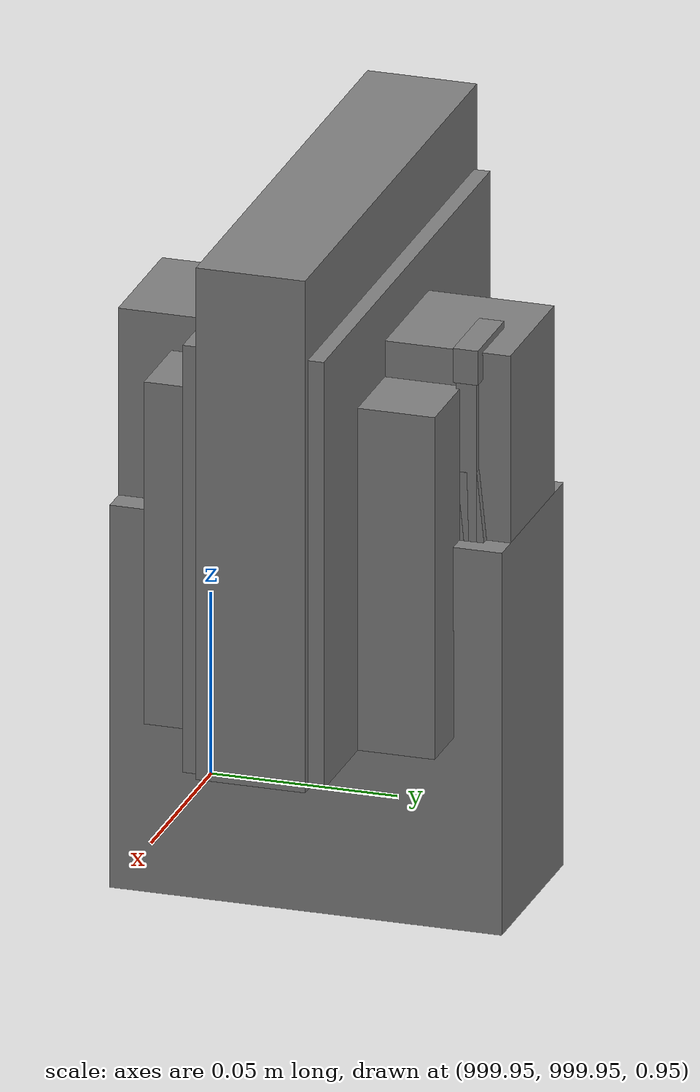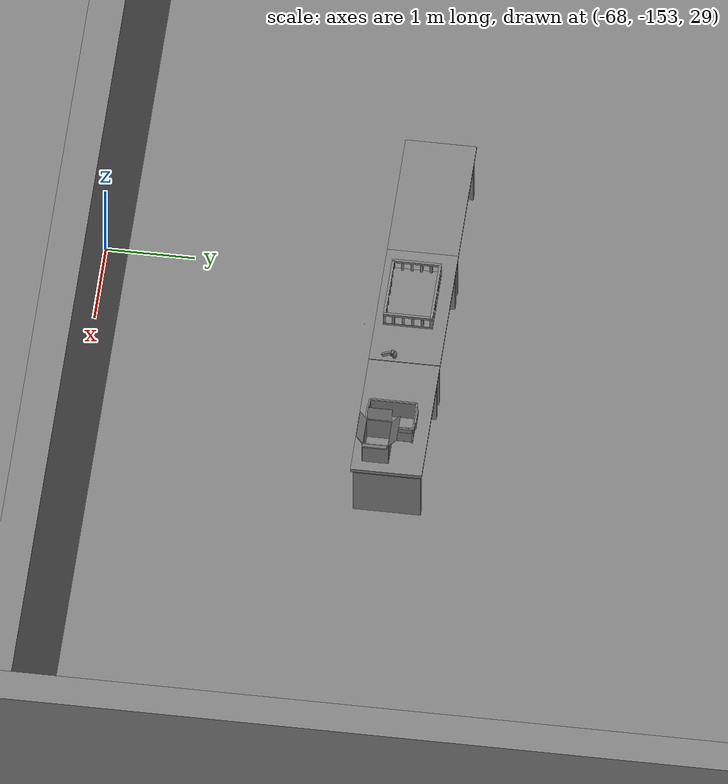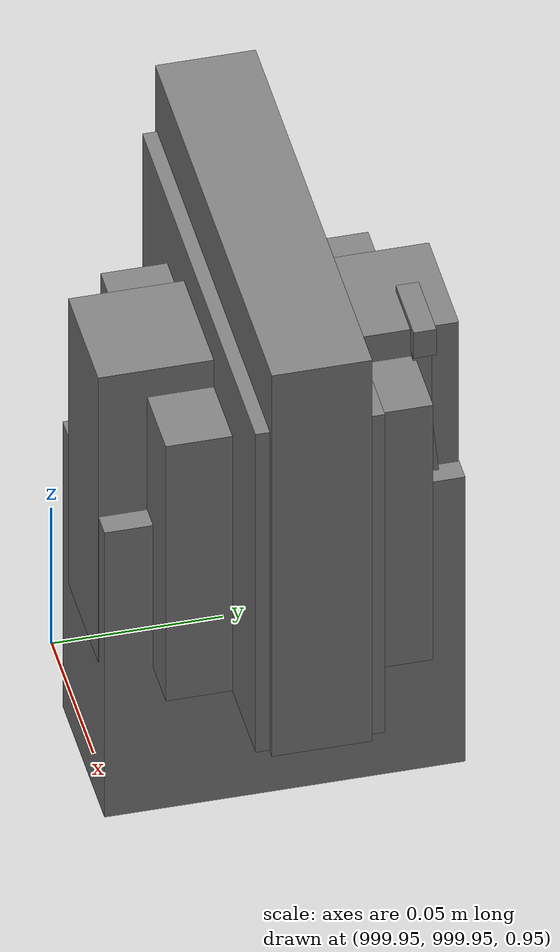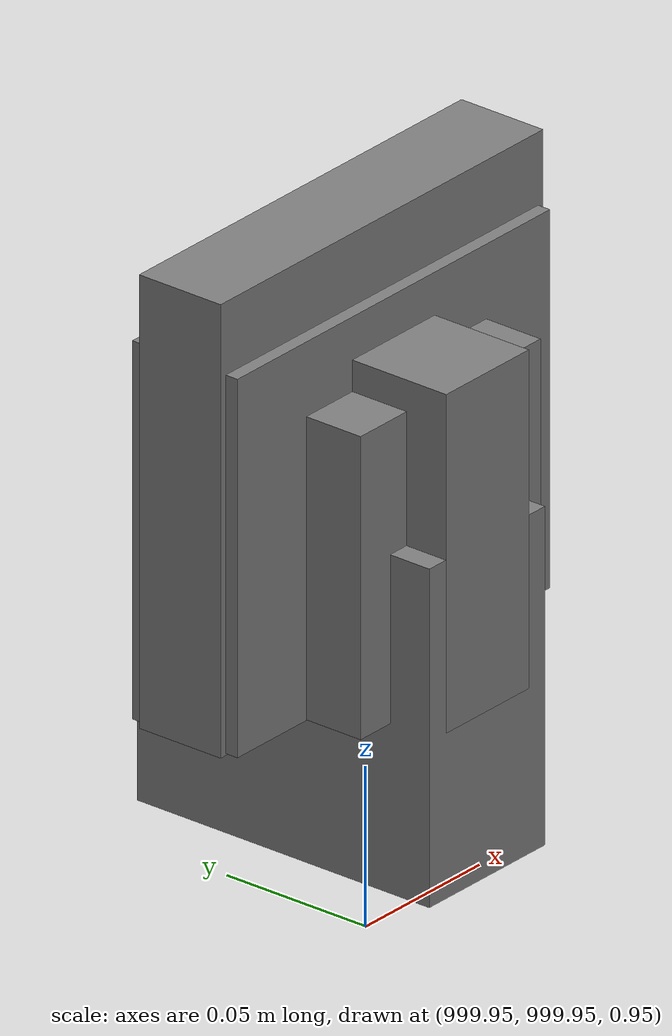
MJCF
<mujoco>
    <option gravity="0.000000000 0.000000000 -9.810000420" timestep="0.0049999999" integrator="implicitfast" density="1.225" viscosity="1.8000001e-05" noslip_iterations="10" iterations="100" sdf_iterations="50">
        <flag multiccd="disable"/>
    </option>
    <size memory="1000M"/>
    <compiler coordinate="local"/>
    <worldbody>
        <light cutoff="30" pos="0 1 1" dir="0 -1 -2"/>
        <light cutoff="30" pos="0 -1 1" dir="0 1 -2"/>
        <body pos="-66.299583435 -149.408142090 31.167484283" euler="121.696891785 -76.737762451 -117.195182800" mocap="true" name="spotlight1_SpotLight"/>
        <body pos="1000.000000000 999.999938965 1.000000000" euler="0.000000000 0.000000000 180.000000000" name="openloong_gripper_2f85_fix_base_usda_intelcore_i5">
            <geom contype="1" conaffinity="1" density="1000" type="box" material="" rgba="0.500000000 0.500000000 0.500000000 1.000000000" solimp="0.899999976 0.949999988 0.001000000" friction="1.000000000 0.005000000 0.000100000" solref="0.020000000 1.000000000" margin="0" condim="3" group="0" pos="0.000000000 0.000000000 0.051722717" quat="0.707106709 0.000000000 0.000000000 -0.707106769" size="0.052800000 0.018080002 0.052800000" name="openloong_gripper_2f85_fix_base_usda_geom_AA117AE9_5DFF_4372_949E_73DBBC103A44"/>
            <freejoint name="openloong_gripper_2f85_fix_base_usda_intelcore_i5_joint"/>
            <site size="0.005000000 0.005000000 0.005000000" rgba="0.500000000 0.500000000 0.500000000 1.000000000" pos="0.000000000 0.000000000 0.000000000" quat="0.999961913 0.008726534 0.000000000 0.000000000" group="0" type="sphere" name="openloong_gripper_2f85_fix_base_usda_intelcore_i5site"/>
        </body>
        <body pos="-65.911788940 -149.421966553 31.168109894" euler="-82.071479797 63.206451416 -114.049713135" mocap="true" name="spotlight6_SpotLight"/>
        <body pos="1000.000000000 1000.000000000 1.000000000" euler="0.000011953 0.000005123 -179.999984741" name="openloong_gripper_2f85_fix_base_usda_intel_box">
            <geom contype="1" conaffinity="1" density="1000" type="box" material="" rgba="0.500000000 0.500000000 0.500000000 1.000000000" solimp="0.899999976 0.949999988 0.001000000" friction="1.000000000 0.005000000 0.000100000" solref="0.020000000 1.000000000" margin="0" condim="3" group="0" pos="0.000000000 -0.000067139 0.000082284" quat="0.707106709 0.000000225 0.000000253 0.707106650" size="0.052800003 0.025300000 0.052800003" name="openloong_gripper_2f85_fix_base_usda_geom_4CAC2369_2531_4355_898C_DC8776105D57"/>
            <freejoint name="openloong_gripper_2f85_fix_base_usda_intel_box_joint"/>
            <site size="0.005000000 0.005000000 0.005000000" rgba="0.500000000 0.500000000 0.500000000 1.000000000" pos="0.000000000 0.000000000 0.000000000" quat="0.999961913 0.008726500 0.000000000 0.000000000" group="0" type="sphere" name="openloong_gripper_2f85_fix_base_usda_intel_boxsite"/>
        </body>
        <body pos="1000.000000000 1000.000000000 1.000000000" euler="0.000000000 0.000000000 180.000000000" name="openloong_gripper_2f85_fix_base_usda_cpu_fan">
            <geom contype="1" conaffinity="1" density="1000" type="box" material="" rgba="0.500000000 0.500000000 0.500000000 1.000000000" solimp="0.899999976 0.949999988 0.001000000" friction="1.000000000 0.005000000 0.000100000" solref="0.020000000 1.000000000" margin="0" condim="3" group="0" pos="0.000000000 0.000000000 0.070034981" quat="0.000000000 0.000000000 0.000000000 1.000000000" size="0.070700005 0.014699999 0.070700005" name="openloong_gripper_2f85_fix_base_usda_geom_D85634D2_D46E_4DBD_AF87_462A09187EB6"/>
            <freejoint name="openloong_gripper_2f85_fix_base_usda_cpu_fan_joint"/>
            <site size="0.005000000 0.005000000 0.005000000" rgba="0.500000000 0.500000000 0.500000000 1.000000000" pos="0.000000000 0.000000000 0.000000000" quat="0.999961913 0.008726535 0.000000000 0.000000000" group="0" type="sphere" name="openloong_gripper_2f85_fix_base_usda_cpu_fancsite"/>
        </body>
        <body pos="1000.000000000 1000.000000000 1.000000000" euler="0.000000000 0.000000000 180.000000000" name="openloong_gripper_2f85_fix_base_usda_wifi_box">
            <geom contype="1" conaffinity="1" density="1000" type="box" material="" rgba="0.500000000 0.500000000 0.500000000 1.000000000" solimp="0.899999976 0.949999988 0.001000000" friction="1.000000000 0.005000000 0.000100000" solref="0.020000000 1.000000000" margin="0" condim="3" group="0" pos="0.000000000 0.000000000 0.058978677" quat="0.000000000 0.000000047 0.000000000 1.000000000" size="0.068499997 0.018999999 0.059000000" name="openloong_gripper_2f85_fix_base_usda_geom_C7876797_3AF8_4EEE_99D9_7D694533B371"/>
            <freejoint name="openloong_gripper_2f85_fix_base_usda_wifi_box_joint"/>
            <site size="0.005000000 0.005000000 0.005000000" rgba="0.500000000 0.500000000 0.500000000 1.000000000" pos="0.000000000 0.000000000 0.000000000" quat="0.999961913 0.008726500 0.000000000 0.000000000" group="0" type="sphere" name="openloong_gripper_2f85_fix_base_usda_wifi_boxsite"/>
        </body>
        <body pos="1000.000000000 1000.000000000 1.000000000" euler="0.000000000 0.000000000 180.000000000" name="openloong_gripper_2f85_fix_base_usda_battery_01">
            <geom contype="1" conaffinity="1" density="1000" type="box" material="" rgba="0.500000000 0.500000000 0.500000000 1.000000000" solimp="0.899999976 0.949999988 0.001000000" friction="1.000000000 0.005000000 0.000100000" solref="0.020000000 1.000000000" margin="0" condim="3" group="0" pos="-0.011123657 -0.041940309 0.101691343" quat="1.000000000 0.000000000 0.000000000 0.000000000" size="0.010800000 0.003375000 0.004725000" name="openloong_gripper_2f85_fix_base_usda_geom_8D05380E_98FF_468B_9335_19D9659DD7AA"/>
            <geom contype="1" conaffinity="1" density="1000" type="box" material="" rgba="0.500000000 0.500000000 0.500000000 1.000000000" solimp="0.899999976 0.949999988 0.001000000" friction="1.000000000 0.005000000 0.000100000" solref="0.020000000 1.000000000" margin="0" condim="3" group="0" pos="-0.010876465 -0.044247437 0.047066893" quat="0.998702705 -0.050920475 0.000000000 0.000000000" size="0.009450001 0.002700000 0.024975000" name="openloong_gripper_2f85_fix_base_usda_geom_81F4153E_58FF_4C5B_9885_2B9C69C34CEE"/>
            <geom contype="1" conaffinity="1" density="1000" type="box" material="" rgba="0.500000000 0.500000000 0.500000000 1.000000000" solimp="0.899999976 0.949999988 0.001000000" friction="1.000000000 0.005000000 0.000100000" solref="0.020000000 1.000000000" margin="0" condim="3" group="0" pos="-0.001235962 -0.000659180 0.047381196" quat="1.000000000 0.000000000 0.000000000 0.000000000" size="0.039420001 0.039150000 0.047250003" name="openloong_gripper_2f85_fix_base_usda_geom_5A97A743_9127_43F6_A775_0D7B0F7075B2"/>
            <geom contype="1" conaffinity="1" density="1000" type="box" material="" rgba="0.500000000 0.500000000 0.500000000 1.000000000" solimp="0.899999976 0.949999988 0.001000000" friction="1.000000000 0.005000000 0.000100000" solref="0.020000000 1.000000000" margin="0" condim="3" group="0" pos="-0.010876465 -0.039138794 0.009851727" quat="1.000000000 0.000000000 0.000000000 0.000000000" size="0.009450001 0.010800000 0.013500000" name="openloong_gripper_2f85_fix_base_usda_geom_E37F478A_68FD_42A0_9B6F_09F8861FFC8C"/>
            <geom contype="1" conaffinity="1" density="1000" type="box" material="" rgba="0.500000000 0.500000000 0.500000000 1.000000000" solimp="0.899999976 0.949999988 0.001000000" friction="1.000000000 0.005000000 0.000100000" solref="0.020000000 1.000000000" margin="0" condim="3" group="0" pos="-0.010876465 -0.041528322 0.071508206" quat="1.000000000 0.000000000 0.000000000 0.000000000" size="0.009450001 0.002700000 0.027000001" name="openloong_gripper_2f85_fix_base_usda_geom_7E67EC2E_52DF_4B44_87F6_332A65E076DE"/>
            <freejoint name="openloong_gripper_2f85_fix_base_usda_battery_01_joint"/>
            <site size="0.005000000 0.005000000 0.005000000" rgba="0.500000000 0.500000000 0.500000000 1.000000000" pos="0.000000000 0.000000000 0.000000000" quat="0.999961913 0.008726500 0.000000000 0.000000000" group="0" type="sphere" name="openloong_gripper_2f85_fix_base_usda_battery_01site"/>
        </body>
        <body pos="-66.055717468 -149.777008057 31.168771744" euler="33.009952545 -87.268257141 43.511821747" mocap="true" name="spotlight2_SpotLight"/>
        <body pos="-64.866622925 -149.383972168 30.183746338" euler="89.999984741 89.999946594 0.000000000" name="openloong_gripper_2f85_fix_base_usda_bluebox_01">
            <geom contype="1" conaffinity="1" density="1000" type="box" material="" rgba="0.500000000 0.500000000 0.500000000 1.000000000" solimp="0.899999976 0.949999988 0.001000000" friction="1.000000000 0.005000000 0.000100000" solref="0.020000000 1.000000000" margin="0" condim="3" group="0" pos="0.276580811 0.187225342 0.000068665" quat="0.707106948 0.000077471 0.707106352 0.000077486" size="0.100000001 0.057999998 0.010000000" name="openloong_gripper_2f85_fix_base_usda_geom_C690492D_AC3A_4402_894D_EB131FB976E7"/>
            <geom contype="1" conaffinity="1" density="1000" type="box" material="" rgba="0.500000000 0.500000000 0.500000000 1.000000000" solimp="0.899999976 0.949999988 0.001000000" friction="1.000000000 0.005000000 0.000100000" solref="0.020000000 1.000000000" margin="0" condim="3" group="0" pos="0.000000000 0.002883911 0.000000000" quat="0.999999881 0.000000000 0.000000000 0.000000000" size="0.254000008 0.003000000 0.172000006" name="openloong_gripper_2f85_fix_base_usda_geom_F5B56BF0_156D_4CEA_9F73_6FA84570FBBA"/>
            <geom contype="1" conaffinity="1" density="1000" type="box" material="" rgba="0.500000000 0.500000000 0.500000000 1.000000000" solimp="0.899999976 0.949999988 0.001000000" friction="1.000000000 0.005000000 0.000100000" solref="0.020000000 1.000000000" margin="0" condim="3" group="0" pos="0.000000000 0.124874115 0.173484802" quat="0.999796331 0.020176515 -0.000000015 0.000000030" size="0.259999990 0.119999997 0.007000000" name="openloong_gripper_2f85_fix_base_usda_geom_2F58A84C_88C8_4BC9_8986_653DA025E71E"/>
            <geom contype="1" conaffinity="1" density="1000" type="box" material="" rgba="0.500000000 0.500000000 0.500000000 1.000000000" solimp="0.899999976 0.949999988 0.001000000" friction="1.000000000 0.005000000 0.000100000" solref="0.020000000 1.000000000" margin="0" condim="3" group="0" pos="0.000000000 0.124874115 -0.173469543" quat="0.999796331 -0.020176545 -0.000000015 0.000000000" size="0.259999990 0.119999997 0.007000000" name="openloong_gripper_2f85_fix_base_usda_geom_678D6115_5111_4A97_AD69_1BABF52AFBAC"/>
            <geom contype="1" conaffinity="1" density="1000" type="box" material="" rgba="0.500000000 0.500000000 0.500000000 1.000000000" solimp="0.899999976 0.949999988 0.001000000" friction="1.000000000 0.005000000 0.000100000" solref="0.020000000 1.000000000" margin="0" condim="3" group="0" pos="0.000000000 0.214008331 0.188980103" quat="0.999912977 0.013176724 0.000000015 0.000000000" size="0.259999990 0.029999999 0.012500000" name="openloong_gripper_2f85_fix_base_usda_geom_E8ECAE31_47DD_4122_B426_6798BC6D432A"/>
            <geom contype="1" conaffinity="1" density="1000" type="box" material="" rgba="0.500000000 0.500000000 0.500000000 1.000000000" solimp="0.899999976 0.949999988 0.001000000" friction="1.000000000 0.005000000 0.000100000" solref="0.020000000 1.000000000" margin="0" condim="3" group="0" pos="-0.258361816 0.125289917 0.001876831" quat="0.702796936 -0.020792112 0.710783124 0.020769298" size="0.189999998 0.119999997 0.009000000" name="openloong_gripper_2f85_fix_base_usda_geom_41E158C6_B3B2_4563_A627_C3F75FFA67D8"/>
            <geom contype="1" conaffinity="1" density="1000" type="box" material="" rgba="0.500000000 0.500000000 0.500000000 1.000000000" solimp="0.899999976 0.949999988 0.001000000" friction="1.000000000 0.005000000 0.000100000" solref="0.020000000 1.000000000" margin="0" condim="3" group="0" pos="0.000000000 0.214008331 -0.188980103" quat="0.999912977 -0.013176769 0.000000030 0.000000015" size="0.259999990 0.029999999 0.012500000" name="openloong_gripper_2f85_fix_base_usda_geom_3B2DF36C_C8E8_45E8_ABE8_C57D27D733DD"/>
            <geom contype="1" conaffinity="1" density="1000" type="box" material="" rgba="0.500000000 0.500000000 0.500000000 1.000000000" solimp="0.899999976 0.949999988 0.001000000" friction="1.000000000 0.005000000 0.000100000" solref="0.020000000 1.000000000" margin="0" condim="3" group="0" pos="-0.276611328 0.187225342 0.000068665" quat="0.707106650 0.000077441 0.707106709 0.000077456" size="0.100000001 0.057999998 0.010000000" name="openloong_gripper_2f85_fix_base_usda_geom_D7913E45_46EA_495F_9AE9_B9BBA0D9EDDB"/>
            <geom contype="1" conaffinity="1" density="1000" type="box" material="" rgba="0.500000000 0.500000000 0.500000000 1.000000000" solimp="0.899999976 0.949999988 0.001000000" friction="1.000000000 0.005000000 0.000100000" solref="0.020000000 1.000000000" margin="0" condim="3" group="0" pos="0.258331299 0.125289917 0.001876831" quat="0.702851415 0.018856421 0.710823774 -0.019329369" size="0.189999998 0.119999997 0.009000000" name="openloong_gripper_2f85_fix_base_usda_geom_D2C2D8FE_0D7E_4C22_A311_A6D9BE0A1625"/>
            <freejoint name="openloong_gripper_2f85_fix_base_usda_bluebox_01_joint"/>
            <site size="0.005000000 0.005000000 0.005000000" rgba="0.500000000 0.500000000 0.500000000 1.000000000" pos="0.000000000 0.000000000 0.000000000" quat="0.999961913 0.008726534 0.000000000 0.000000000" group="0" type="sphere" name="openloong_gripper_2f85_fix_base_usda_bluebox_01site"/>
        </body>
        <body pos="-64.496299744 -149.491867065 30.235729218" euler="0.000000000 0.000000000 89.999946594" name="openloong_gripper_2f85_fix_base_usda_cardboardbox_01">
            <geom contype="1" conaffinity="1" density="1000" type="box" material="" rgba="0.500000000 0.500000000 0.500000000 1.000000000" solimp="0.899999976 0.949999988 0.001000000" friction="1.000000000 0.005000000 0.000100000" solref="0.020000000 1.000000000" margin="0" condim="3" group="0" pos="-0.003166199 -0.004086494 0.005052090" quat="1.000000000 0.000000000 0.000000000 0.000000000" size="0.142499998 0.177500010 0.005000000" name="openloong_gripper_2f85_fix_base_usda_geom_84493284_4D46_4767_996B_A3FE01D25476"/>
            <geom contype="1" conaffinity="1" density="1000" type="box" material="" rgba="0.500000000 0.500000000 0.500000000 1.000000000" solimp="0.899999976 0.949999988 0.001000000" friction="1.000000000 0.005000000 0.000100000" solref="0.020000000 1.000000000" margin="0" condim="3" group="0" pos="-0.003166199 0.170316696 0.150570869" quat="1.000000000 0.000000000 0.000000000 0.000000000" size="0.142499998 0.005000000 0.149999991" name="openloong_gripper_2f85_fix_base_usda_geom_C279587D_29EB_4306_8F7F_F6F521AD4ACA"/>
            <geom contype="1" conaffinity="1" density="1000" type="box" material="" rgba="0.500000000 0.500000000 0.500000000 1.000000000" solimp="0.899999976 0.949999988 0.001000000" friction="1.000000000 0.005000000 0.000100000" solref="0.020000000 1.000000000" margin="0" condim="3" group="0" pos="-0.147399902 -0.005307198 0.150570869" quat="1.000000000 0.000000000 0.000000000 0.000000000" size="0.005000000 0.177500010 0.149999991" name="openloong_gripper_2f85_fix_base_usda_geom_4A579446_4063_4434_95DB_89F95B940332"/>
            <geom contype="1" conaffinity="1" density="1000" type="box" material="" rgba="0.500000000 0.500000000 0.500000000 1.000000000" solimp="0.899999976 0.949999988 0.001000000" friction="1.000000000 0.005000000 0.000100000" solref="0.020000000 1.000000000" margin="0" condim="3" group="0" pos="0.140275955 -0.005307198 0.150570869" quat="1.000000000 0.000000000 0.000000000 0.000000000" size="0.005000000 0.177500010 0.149999991" name="openloong_gripper_2f85_fix_base_usda_geom_E0CA508C_0031_4F72_A4A0_2A9FE985CAEF"/>
            <geom contype="1" conaffinity="1" density="1000" type="box" material="" rgba="0.500000000 0.500000000 0.500000000 1.000000000" solimp="0.899999976 0.949999988 0.001000000" friction="1.000000000 0.005000000 0.000100000" solref="0.020000000 1.000000000" margin="0" condim="3" group="0" pos="-0.003166199 -0.181550980 0.150570869" quat="1.000000000 0.000000000 0.000000000 0.000000000" size="0.142499998 0.005000000 0.149999991" name="openloong_gripper_2f85_fix_base_usda_geom_A35E118B_DCAE_473C_BEBA_2ED847DEFA88"/>
            <freejoint name="openloong_gripper_2f85_fix_base_usda_cardboardbox_01_joint"/>
            <site size="0.005000000 0.005000000 0.005000000" rgba="0.500000000 0.500000000 0.500000000 1.000000000" pos="0.000000000 0.000000000 0.000000000" quat="0.999961913 0.008726535 0.000000000 0.000000000" group="0" type="sphere" name="openloong_gripper_2f85_fix_base_usda_site_78D8FAE4_3068_4BA2_8591_05C3E67DBFBF"/>
            <body pos="0.139160156 -0.004048347 0.301930904" euler="-179.999954224 49.383502960 179.999954224" name="openloong_gripper_2f85_fix_base_usda_A1_006">
                <geom contype="1" conaffinity="1" density="1000" type="box" material="" rgba="0.500000000 0.500000000 0.500000000 1.000000000" solimp="0.899999976 0.949999988 0.001000000" friction="1.000000000 0.005000000 0.000100000" solref="0.020000000 1.000000000" margin="0" condim="3" group="0" pos="-0.071587563 0.000009537 0.001745224" quat="0.999999881 0.000000000 0.000000000 0.000000000" size="0.071249999 0.179999992 0.002500000" name="openloong_gripper_2f85_fix_base_usda_geom_5FF12C59_F1EC_43D2_B002_2ADDE5822816"/>
                <joint armature="0" stiffness="0.07" damping="0.0099999998" axis="0.000000 1.000000 0.000000" type="hinge" name="openloong_gripper_2f85_fix_base_usda_A1_006"/>
            </body>
            <body pos="-0.145902634 -0.004086494 0.301938057" euler="-180.000000000 -60.000011444 -180.000000000" name="openloong_gripper_2f85_fix_base_usda_A2_006">
                <geom contype="1" conaffinity="1" density="1000" type="box" material="" rgba="0.500000000 0.500000000 0.500000000 1.000000000" solimp="0.899999976 0.949999988 0.001000000" friction="1.000000000 0.005000000 0.000100000" solref="0.020000000 1.000000000" margin="0" condim="3" group="0" pos="0.071268082 0.000009537 0.002717972" quat="0.000002921 0.000000000 -0.000000030 0.999999881" size="0.071249999 0.179999992 0.002500000" name="openloong_gripper_2f85_fix_base_usda_geom_867781F1_B47A_4881_8ACA_91EE22F0059A"/>
                <joint armature="0" stiffness="0.07" damping="0.0099999998" axis="0.000000 1.000000 0.000000" type="hinge" name="openloong_gripper_2f85_fix_base_usda_A2_006"/>
            </body>
            <body pos="-0.003385544 0.175991058 0.301930904" euler="-125.858116150 -0.000004561 0.000002331" name="openloong_gripper_2f85_fix_base_usda_B2_006">
                <geom contype="1" conaffinity="1" density="1000" type="box" material="" rgba="0.500000000 0.500000000 0.500000000 1.000000000" solimp="0.899999976 0.949999988 0.001000000" friction="1.000000000 0.005000000 0.000100000" solref="0.020000000 1.000000000" margin="0" condim="3" group="0" pos="0.000009537 -0.070939064 -0.002470016" quat="0.999614120 0.027776197 -0.000000015 0.000000030" size="0.137500003 0.064999998 0.005000000" name="openloong_gripper_2f85_fix_base_usda_geom_E9DDB660_63E1_4335_AEC0_F8D747B6AA2B"/>
                <joint armature="0" stiffness="0.07" damping="0.0099999998" axis="1.000000 0.000000 0.000000" type="hinge" name="openloong_gripper_2f85_fix_base_usda_B2_006"/>
            </body>
            <body pos="-0.003385544 -0.184140205 0.301938057" euler="147.805557251 0.000000000 0.000000000" name="openloong_gripper_2f85_fix_base_usda_B1_006">
                <geom contype="1" conaffinity="1" density="1000" type="box" material="" rgba="0.500000000 0.500000000 0.500000000 1.000000000" solimp="0.899999976 0.949999988 0.001000000" friction="1.000000000 0.005000000 0.000100000" solref="0.020000000 1.000000000" margin="0" condim="3" group="0" pos="-0.000028610 0.070202351 -0.002703667" quat="0.999614179 -0.027776167 0.000000000 0.000000000" size="0.137500003 0.064999998 0.005000000" name="openloong_gripper_2f85_fix_base_usda_geom_84704FA8_436B_4842_BB8A_422549E2D265"/>
                <joint armature="0" stiffness="0.07" damping="0.0099999998" axis="1.000000 0.000000 0.000000" type="hinge" name="openloong_gripper_2f85_fix_base_usda_B1_006"/>
            </body>
        </body>
        <body pos="-65.882858276 -149.481979370 30.229999542" euler="-64.487716675 0.000000000 0.000000000" name="openloong_gripper_2f85_fix_base_usda_Barcode">
            <geom contype="1" conaffinity="1" density="1000" type="box" material="" rgba="0.500000000 0.500000000 0.500000000 1.000000000" solimp="0.899999976 0.949999988 0.001000000" friction="1.000000000 0.005000000 0.000100000" solref="0.020000000 1.000000000" margin="0" condim="3" group="0" pos="0.000000000 0.013038635 0.001419067" quat="0.000000000 0.000000000 0.000000000 1.000000119" size="0.034000002 0.010000000 0.017999999" name="openloong_gripper_2f85_fix_base_usda_geom_C5B40697_58C0_4C39_A4EC_144EF2B03172"/>
            <geom contype="1" conaffinity="1" density="1000" type="box" material="" rgba="0.500000000 0.500000000 0.500000000 1.000000000" solimp="0.899999976 0.949999988 0.001000000" friction="1.000000000 0.005000000 0.000100000" solref="0.020000000 1.000000000" margin="0" condim="3" group="0" pos="0.000000000 -0.035301208 -0.007095337" quat="0.000000000 0.000000000 -0.043619365 0.999048233" size="0.028999999 0.010000000 0.020000000" name="openloong_gripper_2f85_fix_base_usda_geom_19DB0D2C_7430_4460_8AE3_E9E5299D59C7"/>
            <geom contype="1" conaffinity="1" density="1000" type="box" material="" rgba="0.500000000 0.500000000 0.500000000 1.000000000" solimp="0.899999976 0.949999988 0.001000000" friction="1.000000000 0.005000000 0.000100000" solref="0.020000000 1.000000000" margin="0" condim="3" group="0" pos="0.000000000 -0.043411255 -0.011749268" quat="0.922262907 0.386563420 0.000000000 0.000000000" size="0.026000001 0.010000000 0.020000000" name="openloong_gripper_2f85_fix_base_usda_geom_E881169D_DAF3_4CC6_9F95_7CEEE787E34F"/>
            <geom contype="1" conaffinity="1" density="1000" type="box" material="" rgba="0.500000000 0.500000000 0.500000000 1.000000000" solimp="0.899999976 0.949999988 0.001000000" friction="1.000000000 0.005000000 0.000100000" solref="0.020000000 1.000000000" margin="0" condim="3" group="0" pos="0.000000000 -0.016967773 -0.031860352" quat="0.000000000 0.000000000 0.000000000 1.000000119" size="0.008000000 0.010000000 0.013000000" name="openloong_gripper_2f85_fix_base_usda_geom_A0B8D02F_E6AD_401C_B38D_A3485CA3725D"/>
            <geom contype="1" conaffinity="1" density="1000" type="box" material="" rgba="0.500000000 0.500000000 0.500000000 1.000000000" solimp="0.899999976 0.949999988 0.001000000" friction="1.000000000 0.005000000 0.000100000" solref="0.020000000 1.000000000" margin="0" condim="3" group="0" pos="0.000000000 -0.001869202 0.000312805" quat="0.953716993 0.300705761 0.000000000 0.000000000" size="0.032000002 0.010000000 0.018999999" name="openloong_gripper_2f85_fix_base_usda_geom_D25BF08D_2972_4F9C_BC26_C5E1FA9C2A02"/>
            <geom contype="1" conaffinity="1" density="1000" type="box" material="" rgba="0.500000000 0.500000000 0.500000000 1.000000000" solimp="0.899999976 0.949999988 0.001000000" friction="1.000000000 0.005000000 0.000100000" solref="0.020000000 1.000000000" margin="0" condim="3" group="0" pos="0.000000000 -0.019531250 -0.003173828" quat="0.953716993 0.300705761 0.000000000 0.000000000" size="0.030999999 0.010000000 0.020000000" name="openloong_gripper_2f85_fix_base_usda_geom_EBFB79EA_6028_4E03_8B7A_705FB7285E54"/>
            <geom contype="1" conaffinity="1" density="1000" type="box" material="" rgba="0.500000000 0.500000000 0.500000000 1.000000000" solimp="0.899999976 0.949999988 0.001000000" friction="1.000000000 0.005000000 0.000100000" solref="0.020000000 1.000000000" margin="0" condim="3" group="0" pos="0.000000000 -0.035301208 -0.007095337" quat="0.953716993 0.300705761 0.000000000 0.000000000" size="0.028999999 0.010000000 0.020000000" name="openloong_gripper_2f85_fix_base_usda_geom_AA85BBF4_17C3_4567_9096_0A831918CE07"/>
            <geom contype="1" conaffinity="1" density="1000" type="box" material="" rgba="0.500000000 0.500000000 0.500000000 1.000000000" solimp="0.899999976 0.949999988 0.001000000" friction="1.000000000 0.005000000 0.000100000" solref="0.020000000 1.000000000" margin="0" condim="3" group="0" pos="0.000000000 -0.042617798 -0.071121216" quat="0.000000000 0.000000000 0.000000000 1.000000119" size="0.013000000 0.021000000 0.059999999" name="openloong_gripper_2f85_fix_base_usda_geom_0365D2AA_10C8_4AAE_9142_E4AF2FC6ED70"/>
            <freejoint name="openloong_gripper_2f85_fix_base_usda_Barcode_joint"/>
            <site size="0.005000000 0.005000000 0.005000000" rgba="0.500000000 0.500000000 0.500000000 1.000000000" pos="0.000000000 0.000000000 0.000000000" quat="1.000000000 0.000000000 0.000000000 0.000000000" group="0" type="sphere" name="openloong_gripper_2f85_fix_base_usda_Barcode_site"/>
        </body>
        <body pos="-66.745018005 -149.392349243 30.184000015" euler="0.000000000 0.000000000 89.999946594" name="[22329959564002]_Basket_01">
            <geom contype="1" conaffinity="1" density="1000" type="box" material="" rgba="0.500000000 0.500000000 0.500000000 1.000000000" solimp="0.899999976 0.949999988 0.001000000" friction="1.000000000 0.005000000 0.000100000" solref="0.020000000 1.000000000" margin="0" condim="3" group="0" pos="-0.052425385 0.389207840 0.089787483" quat="0.707107008 0.000000000 0.000000000 0.707106411" size="0.014249999 0.014249999 0.059999999" name="[22329959564002]_geom_8336EAF6_D647_40FB_9701_BCE747E36EB3"/>
            <geom contype="1" conaffinity="1" density="1000" type="box" material="" rgba="0.500000000 0.500000000 0.500000000 1.000000000" solimp="0.899999976 0.949999988 0.001000000" friction="1.000000000 0.005000000 0.000100000" solref="0.020000000 1.000000000" margin="0" condim="3" group="0" pos="0.264015198 -0.133043289 0.089787483" quat="0.707107008 0.000000000 0.000000000 0.707106411" size="0.014249999 0.014249999 0.059999999" name="[22329959564002]_geom_8DE84C14_12E6_4D90_AD66_0BC0CF2E1C19"/>
            <geom contype="1" conaffinity="1" density="1000" type="box" material="" rgba="0.500000000 0.500000000 0.500000000 1.000000000" solimp="0.899999976 0.949999988 0.001000000" friction="1.000000000 0.005000000 0.000100000" solref="0.020000000 1.000000000" margin="0" condim="3" group="0" pos="-0.264015198 -0.265548706 0.089793205" quat="0.707107008 0.000000000 0.000000000 0.707106411" size="0.014249999 0.014249999 0.059999999" name="[22329959564002]_geom_30EF4D03_AD56_4215_BF4C_40B3042CEBF3"/>
            <geom contype="1" conaffinity="1" density="1000" type="box" material="" rgba="0.500000000 0.500000000 0.500000000 1.000000000" solimp="0.899999976 0.949999988 0.001000000" friction="1.000000000 0.005000000 0.000100000" solref="0.020000000 1.000000000" margin="0" condim="3" group="0" pos="-0.160263062 -0.389322281 0.089793205" quat="0.707107008 0.000000000 0.000000000 0.707106411" size="0.014249999 0.014249999 0.059999999" name="[22329959564002]_geom_BD6D50E5_0376_4BFC_8A88_5A64A48605E0"/>
            <geom contype="1" conaffinity="1" density="1000" type="box" material="" rgba="0.500000000 0.500000000 0.500000000 1.000000000" solimp="0.899999976 0.949999988 0.001000000" friction="1.000000000 0.005000000 0.000100000" solref="0.020000000 1.000000000" margin="0" condim="3" group="0" pos="0.162265778 -0.389322281 0.089787483" quat="0.707107008 0.000000000 0.000000000 0.707106411" size="0.014249999 0.014249999 0.059999999" name="[22329959564002]_geom_0D3BC290_18DF_47B9_AA5A_019E24AC34E4"/>
            <geom contype="1" conaffinity="1" density="1000" type="box" material="" rgba="0.500000000 0.500000000 0.500000000 1.000000000" solimp="0.899999976 0.949999988 0.001000000" friction="1.000000000 0.005000000 0.000100000" solref="0.020000000 1.000000000" margin="0" condim="3" group="0" pos="0.264015198 0.389207840 0.089787483" quat="0.707107008 0.000000000 0.000000000 0.707106411" size="0.014249999 0.014249999 0.059999999" name="[22329959564002]_geom_956B44E9_4285_4532_9767_F2C8B39BFDFA"/>
            <geom contype="1" conaffinity="1" density="1000" type="box" material="" rgba="0.500000000 0.500000000 0.500000000 1.000000000" solimp="0.899999976 0.949999988 0.001000000" friction="1.000000000 0.005000000 0.000100000" solref="0.020000000 1.000000000" margin="0" condim="3" group="0" pos="-0.264015198 -0.133043289 0.089793205" quat="0.707107008 0.000000000 0.000000000 0.707106411" size="0.014249999 0.014249999 0.059999999" name="[22329959564002]_geom_A7EBD3EF_2962_404F_AD15_7AE38B174F21"/>
            <geom contype="1" conaffinity="1" density="1000" type="box" material="" rgba="0.500000000 0.500000000 0.500000000 1.000000000" solimp="0.899999976 0.949999988 0.001000000" friction="1.000000000 0.005000000 0.000100000" solref="0.020000000 1.000000000" margin="0" condim="3" group="0" pos="-0.264026642 0.269256592 0.089793205" quat="0.707107008 0.000000000 0.000000000 0.707106411" size="0.014249999 0.014249999 0.059999999" name="[22329959564002]_geom_3493F680_6B44_443A_A4F3_564C7DCF7E99"/>
            <geom contype="1" conaffinity="1" density="1000" type="box" material="" rgba="0.500000000 0.500000000 0.500000000 1.000000000" solimp="0.899999976 0.949999988 0.001000000" friction="1.000000000 0.005000000 0.000100000" solref="0.020000000 1.000000000" margin="0" condim="3" group="0" pos="0.054462433 0.389207840 0.089787483" quat="0.707107008 0.000000000 0.000000000 0.707106411" size="0.014249999 0.014249999 0.059999999" name="[22329959564002]_geom_71C24EA4_B34B_4CDB_A6EF_8D4F4EE08ACE"/>
            <geom contype="1" conaffinity="1" density="1000" type="box" material="" rgba="0.500000000 0.500000000 0.500000000 1.000000000" solimp="0.899999976 0.949999988 0.001000000" friction="1.000000000 0.005000000 0.000100000" solref="0.020000000 1.000000000" margin="0" condim="3" group="0" pos="0.054462433 -0.389322281 0.089787483" quat="0.707107008 0.000000000 0.000000000 0.707106411" size="0.014249999 0.014249999 0.059999999" name="[22329959564002]_geom_992256A4_5CC9_42BB_8DCD_048448235CD7"/>
            <geom contype="1" conaffinity="1" density="1000" type="box" material="" rgba="0.500000000 0.500000000 0.500000000 1.000000000" solimp="0.899999976 0.949999988 0.001000000" friction="1.000000000 0.005000000 0.000100000" solref="0.020000000 1.000000000" margin="0" condim="3" group="0" pos="0.264015198 0.269256592 0.089793205" quat="0.707107008 0.000000000 0.000000000 0.707106411" size="0.014249999 0.014249999 0.059999999" name="[22329959564002]_geom_3E9C7143_399F_4AB2_B061_B2D884DEA287"/>
            <geom contype="1" conaffinity="1" density="1000" type="box" material="" rgba="0.500000000 0.500000000 0.500000000 1.000000000" solimp="0.899999976 0.949999988 0.001000000" friction="1.000000000 0.005000000 0.000100000" solref="0.020000000 1.000000000" margin="0" condim="3" group="0" pos="0.264015198 -0.389322281 0.089787483" quat="0.707107008 0.000000000 0.000000000 0.707106411" size="0.014249999 0.014249999 0.059999999" name="[22329959564002]_geom_B3B9126D_EE29_4D88_B181_67380B93FCFD"/>
            <geom contype="1" conaffinity="1" density="1000" type="box" material="" rgba="0.500000000 0.500000000 0.500000000 1.000000000" solimp="0.899999976 0.949999988 0.001000000" friction="1.000000000 0.005000000 0.000100000" solref="0.020000000 1.000000000" margin="0" condim="3" group="0" pos="0.000000000 0.000000000 0.015998840" quat="0.707107008 0.000000000 0.000000000 0.707106411" size="0.403499991 0.279000014 0.015750000" name="[22329959564002]_geom_18C575C2_32B4_4C49_B9B0_E6B209082CB5"/>
            <geom contype="1" conaffinity="1" density="1000" type="box" material="" rgba="0.500000000 0.500000000 0.500000000 1.000000000" solimp="0.899999976 0.949999988 0.001000000" friction="1.000000000 0.005000000 0.000100000" solref="0.020000000 1.000000000" margin="0" condim="3" group="0" pos="0.000000000 -0.389476776 0.163619041" quat="0.707107008 0.000000000 0.000000000 0.707106411" size="0.015000000 0.277500004 0.015750000" name="[22329959564002]_geom_50EE4AAB_A3BB_4CB9_86B7_E250AD9FA10B"/>
            <geom contype="1" conaffinity="1" density="1000" type="box" material="" rgba="0.500000000 0.500000000 0.500000000 1.000000000" solimp="0.899999976 0.949999988 0.001000000" friction="1.000000000 0.005000000 0.000100000" solref="0.020000000 1.000000000" margin="0" condim="3" group="0" pos="0.162265778 0.389207840 0.089787483" quat="0.707107008 0.000000000 0.000000000 0.707106411" size="0.014249999 0.014249999 0.059999999" name="[22329959564002]_geom_4D62A2B7_8513_4456_9E34_C0C3BC19FE74"/>
            <geom contype="1" conaffinity="1" density="1000" type="box" material="" rgba="0.500000000 0.500000000 0.500000000 1.000000000" solimp="0.899999976 0.949999988 0.001000000" friction="1.000000000 0.005000000 0.000100000" solref="0.020000000 1.000000000" margin="0" condim="3" group="0" pos="0.000000000 0.389471054 0.163619041" quat="0.707107008 0.000000000 0.000000000 0.707106411" size="0.015000000 0.277500004 0.015750000" name="[22329959564002]_geom_A76C048F_CE72_45F5_9A94_A0C56F239F56"/>
            <geom contype="1" conaffinity="1" density="1000" type="box" material="" rgba="0.500000000 0.500000000 0.500000000 1.000000000" solimp="0.899999976 0.949999988 0.001000000" friction="1.000000000 0.005000000 0.000100000" solref="0.020000000 1.000000000" margin="0" condim="3" group="0" pos="-0.263511658 0.000000000 0.163619041" quat="0.707107008 0.000000000 0.000000000 0.707106411" size="0.403499991 0.015000000 0.015750000" name="[22329959564002]_geom_94471826_E204_4C2A_82A2_39DFF3BE2E6C"/>
            <geom contype="1" conaffinity="1" density="1000" type="box" material="" rgba="0.500000000 0.500000000 0.500000000 1.000000000" solimp="0.899999976 0.949999988 0.001000000" friction="1.000000000 0.005000000 0.000100000" solref="0.020000000 1.000000000" margin="0" condim="3" group="0" pos="-0.264015198 0.141334534 0.089793205" quat="0.707107008 0.000000000 0.000000000 0.707106411" size="0.014249999 0.014249999 0.059999999" name="[22329959564002]_geom_AEBC8CC2_4BE8_43E9_982A_A2E7143CFB95"/>
            <geom contype="1" conaffinity="1" density="1000" type="box" material="" rgba="0.500000000 0.500000000 0.500000000 1.000000000" solimp="0.899999976 0.949999988 0.001000000" friction="1.000000000 0.005000000 0.000100000" solref="0.020000000 1.000000000" margin="0" condim="3" group="0" pos="0.264015198 -0.265548706 0.089787483" quat="0.707107008 0.000000000 0.000000000 0.707106411" size="0.014249999 0.014249999 0.059999999" name="[22329959564002]_geom_7C273F01_0428_4A21_9CF4_55B6ECFCE368"/>
            <geom contype="1" conaffinity="1" density="1000" type="box" material="" rgba="0.500000000 0.500000000 0.500000000 1.000000000" solimp="0.899999976 0.949999988 0.001000000" friction="1.000000000 0.005000000 0.000100000" solref="0.020000000 1.000000000" margin="0" condim="3" group="0" pos="-0.160263062 0.389207840 0.089787483" quat="0.707107008 0.000000000 0.000000000 0.707106411" size="0.014249999 0.014249999 0.059999999" name="[22329959564002]_geom_5D53413C_3815_4F5A_9D26_28EBE25A0B6F"/>
            <geom contype="1" conaffinity="1" density="1000" type="box" material="" rgba="0.500000000 0.500000000 0.500000000 1.000000000" solimp="0.899999976 0.949999988 0.001000000" friction="1.000000000 0.005000000 0.000100000" solref="0.020000000 1.000000000" margin="0" condim="3" group="0" pos="-0.052425385 -0.389322281 0.089787483" quat="0.707107008 0.000000000 0.000000000 0.707106411" size="0.014249999 0.014249999 0.059999999" name="[22329959564002]_geom_5C5003FE_BDFD_44F5_B506_F9F69BEDBB1D"/>
            <geom contype="1" conaffinity="1" density="1000" type="box" material="" rgba="0.500000000 0.500000000 0.500000000 1.000000000" solimp="0.899999976 0.949999988 0.001000000" friction="1.000000000 0.005000000 0.000100000" solref="0.020000000 1.000000000" margin="0" condim="3" group="0" pos="-0.264026642 -0.389322281 0.089793205" quat="0.707107008 0.000000000 0.000000000 0.707106411" size="0.014249999 0.014249999 0.059999999" name="[22329959564002]_geom_202026C4_2022_400B_BF40_33374AF6B2A2"/>
            <geom contype="1" conaffinity="1" density="1000" type="box" material="" rgba="0.500000000 0.500000000 0.500000000 1.000000000" solimp="0.899999976 0.949999988 0.001000000" friction="1.000000000 0.005000000 0.000100000" solref="0.020000000 1.000000000" margin="0" condim="3" group="0" pos="0.264015198 0.141334534 0.089787483" quat="0.707107008 0.000000000 0.000000000 0.707106411" size="0.014249999 0.014249999 0.059999999" name="[22329959564002]_geom_76426ACA_76FA_463C_BE38_DFEDA17E3398"/>
            <geom contype="1" conaffinity="1" density="1000" type="box" material="" rgba="0.500000000 0.500000000 0.500000000 1.000000000" solimp="0.899999976 0.949999988 0.001000000" friction="1.000000000 0.005000000 0.000100000" solref="0.020000000 1.000000000" margin="0" condim="3" group="0" pos="-0.264015198 0.389207840 0.089793205" quat="0.707107008 0.000000000 0.000000000 0.707106411" size="0.014249999 0.014249999 0.059999999" name="[22329959564002]_geom_64CA1333_9DD2_4CED_BCCB_4E42840F0C04"/>
            <geom contype="1" conaffinity="1" density="1000" type="box" material="" rgba="0.500000000 0.500000000 0.500000000 1.000000000" solimp="0.899999976 0.949999988 0.001000000" friction="1.000000000 0.005000000 0.000100000" solref="0.020000000 1.000000000" margin="0" condim="3" group="0" pos="0.264015198 0.004480362 0.089787483" quat="0.707107008 0.000000000 0.000000000 0.707106411" size="0.014249999 0.014249999 0.059999999" name="[22329959564002]_geom_5F3E6304_AA7C_4E7A_B79E_E2548A01DF04"/>
            <geom contype="1" conaffinity="1" density="1000" type="box" material="" rgba="0.500000000 0.500000000 0.500000000 1.000000000" solimp="0.899999976 0.949999988 0.001000000" friction="1.000000000 0.005000000 0.000100000" solref="0.020000000 1.000000000" margin="0" condim="3" group="0" pos="0.263694763 -0.000011444 0.163619041" quat="0.707107008 0.000000000 0.000000000 0.707106411" size="0.403499991 0.015000000 0.015750000" name="[22329959564002]_geom_22506155_3A5A_4F2A_BBCD_AB642AFEB5F1"/>
            <geom contype="1" conaffinity="1" density="1000" type="box" material="" rgba="0.500000000 0.500000000 0.500000000 1.000000000" solimp="0.899999976 0.949999988 0.001000000" friction="1.000000000 0.005000000 0.000100000" solref="0.020000000 1.000000000" margin="0" condim="3" group="0" pos="-0.264015198 0.004480362 0.089793205" quat="0.707107008 0.000000000 0.000000000 0.707106411" size="0.014249999 0.014249999 0.059999999" name="[22329959564002]_geom_B206F299_392A_4C47_9882_35A8AF5D259F"/>
            <freejoint name="[22329959564002]_joint_E6C9CCAF_A204_4BA3_B4A2_C8785D0D4E74"/>
        </body>
        <body pos="0.000000000 0.000000000 0.000000000" euler="0.000000000 0.000000000 0.000000000" name="Static Objects_Static Objects">
            <geom contype="1" conaffinity="1" density="1000" type="box" material="" rgba="0.500000000 0.500000000 0.500000000 1.000000000" solimp="0.899999976 0.949999988 0.001000000" friction="1.000000000 0.005000000 0.000100000" solref="0.020000000 1.000000000" margin="0" condim="3" group="0" pos="-67.544113159 -149.365814209 29.727830887" quat="0.500000417 0.499999970 0.499999553 0.499999970" size="0.381000012 0.319999993 0.041000001" name="Static Objects_geom_2CE8F9ED_F1AE_43B2_AF77_334D0F6D245F"/>
            <geom contype="1" conaffinity="1" density="1000" type="box" material="" rgba="0.500000000 0.500000000 0.500000000 1.000000000" solimp="0.899999976 0.949999988 0.001000000" friction="1.000000000 0.005000000 0.000100000" solref="0.020000000 1.000000000" margin="0" condim="3" group="0" pos="-68.239501953 -149.365814209 30.086868286" quat="0.500000417 0.499999970 0.499999553 0.499999970" size="0.370999992 0.039500002 0.745000005" name="Static Objects_geom_39DB4911_7729_4C13_8996_2E52796F8875"/>
            <geom contype="1" conaffinity="1" density="1000" type="box" material="" rgba="0.500000000 0.500000000 0.500000000 1.000000000" solimp="0.899999976 0.949999988 0.001000000" friction="1.000000000 0.005000000 0.000100000" solref="0.020000000 1.000000000" margin="0" condim="3" group="0" pos="-68.239501953 -149.365814209 30.147235870" quat="0.500000417 0.499999970 0.499999553 0.499999970" size="0.400000006 0.022000000 0.800000012" name="Static Objects_geom_38397ADD_7760_4FDC_927C_9A69EFED5B8D"/>
            <geom contype="1" conaffinity="1" density="1000" type="box" material="" rgba="0.500000000 0.500000000 0.500000000 1.000000000" solimp="0.899999976 0.949999988 0.001000000" friction="1.000000000 0.005000000 0.000100000" solref="0.020000000 1.000000000" margin="0" condim="3" group="0" pos="-68.934890747 -149.365814209 29.727830887" quat="0.500000417 0.499999970 0.499999553 0.499999970" size="0.381000012 0.319999993 0.041000001" name="Static Objects_geom_1EA777C7_8C31_4EE6_A92F_8EB6797E3A5C"/>
            <geom contype="1" conaffinity="1" density="1000" type="box" material="" rgba="0.500000000 0.500000000 0.500000000 1.000000000" solimp="0.899999976 0.949999988 0.001000000" friction="1.000000000 0.005000000 0.000100000" solref="0.020000000 1.000000000" margin="0" condim="3" group="0" pos="-68.239501953 -149.365814209 29.561563492" quat="0.500000417 0.499999970 0.499999553 0.499999970" size="0.020000000 0.022000000 0.660000026" name="Static Objects_geom_15E6B040_0B6B_46BC_96E8_D329849C91F0"/>
            <geom contype="1" conaffinity="1" density="1000" type="box" material="" rgba="0.500000000 0.500000000 0.500000000 1.000000000" solimp="0.899999976 0.949999988 0.001000000" friction="1.000000000 0.005000000 0.000100000" solref="0.020000000 1.000000000" margin="0" condim="3" group="0" pos="-65.945671082 -149.365814209 29.727830887" quat="0.500000417 0.499999970 0.499999553 0.499999970" size="0.381000012 0.319999993 0.041000001" name="Static Objects_geom_62C2528E_6C9C_4AD4_B51D_BD5EF831FF0F"/>
            <geom contype="1" conaffinity="1" density="1000" type="box" material="" rgba="0.500000000 0.500000000 0.500000000 1.000000000" solimp="0.899999976 0.949999988 0.001000000" friction="1.000000000 0.005000000 0.000100000" solref="0.020000000 1.000000000" margin="0" condim="3" group="0" pos="-66.641059875 -149.365814209 30.086868286" quat="0.500000417 0.499999970 0.499999553 0.499999970" size="0.370999992 0.039500002 0.745000005" name="Static Objects_geom_EEF35D84_8453_48A5_B27D_B566C6B400E7"/>
            <geom contype="1" conaffinity="1" density="1000" type="box" material="" rgba="0.500000000 0.500000000 0.500000000 1.000000000" solimp="0.899999976 0.949999988 0.001000000" friction="1.000000000 0.005000000 0.000100000" solref="0.020000000 1.000000000" margin="0" condim="3" group="0" pos="-66.641059875 -149.365814209 30.147235870" quat="0.500000417 0.499999970 0.499999553 0.499999970" size="0.400000006 0.022000000 0.800000012" name="Static Objects_geom_EA32099D_EB25_4A63_8023_8AFE8B228455"/>
            <geom contype="1" conaffinity="1" density="1000" type="box" material="" rgba="0.500000000 0.500000000 0.500000000 1.000000000" solimp="0.899999976 0.949999988 0.001000000" friction="1.000000000 0.005000000 0.000100000" solref="0.020000000 1.000000000" margin="0" condim="3" group="0" pos="-67.336448669 -149.365814209 29.727830887" quat="0.500000417 0.499999970 0.499999553 0.499999970" size="0.381000012 0.319999993 0.041000001" name="Static Objects_geom_F4E5C085_EFDE_4098_B68F_D2779BF86C62"/>
            <geom contype="1" conaffinity="1" density="1000" type="box" material="" rgba="0.500000000 0.500000000 0.500000000 1.000000000" solimp="0.899999976 0.949999988 0.001000000" friction="1.000000000 0.005000000 0.000100000" solref="0.020000000 1.000000000" margin="0" condim="3" group="0" pos="-66.641059875 -149.365814209 29.561563492" quat="0.500000417 0.499999970 0.499999553 0.499999970" size="0.020000000 0.022000000 0.660000026" name="Static Objects_geom_5CA9939D_9059_4742_BA3C_A63C194F7C61"/>
            <geom contype="1" conaffinity="1" density="1000" type="box" material="" rgba="0.500000000 0.500000000 0.500000000 1.000000000" solimp="0.899999976 0.949999988 0.001000000" friction="1.000000000 0.005000000 0.000100000" solref="0.020000000 1.000000000" margin="0" condim="3" group="0" pos="-64.338577271 -149.365814209 29.727830887" quat="0.500000417 0.499999970 0.499999553 0.499999970" size="0.381000012 0.319999993 0.041000001" name="Static Objects_geom_8796FD1D_34F5_4BEC_A9FB_B9BF7A18BBCD"/>
            <geom contype="1" conaffinity="1" density="1000" type="box" material="" rgba="0.500000000 0.500000000 0.500000000 1.000000000" solimp="0.899999976 0.949999988 0.001000000" friction="1.000000000 0.005000000 0.000100000" solref="0.020000000 1.000000000" margin="0" condim="3" group="0" pos="-65.033966064 -149.365814209 30.086868286" quat="0.500000417 0.499999970 0.499999553 0.499999970" size="0.370999992 0.039500002 0.745000005" name="Static Objects_geom_C4B516C6_5CB5_450A_B8BE_CCBC4145E105"/>
            <geom contype="1" conaffinity="1" density="1000" type="box" material="" rgba="0.500000000 0.500000000 0.500000000 1.000000000" solimp="0.899999976 0.949999988 0.001000000" friction="1.000000000 0.005000000 0.000100000" solref="0.020000000 1.000000000" margin="0" condim="3" group="0" pos="-65.033966064 -149.365814209 30.147235870" quat="0.500000417 0.499999970 0.499999553 0.499999970" size="0.400000006 0.022000000 0.800000012" name="Static Objects_geom_0630DEAD_0CE2_4252_A34D_AC99FF2A4AC4"/>
            <geom contype="1" conaffinity="1" density="1000" type="box" material="" rgba="0.500000000 0.500000000 0.500000000 1.000000000" solimp="0.899999976 0.949999988 0.001000000" friction="1.000000000 0.005000000 0.000100000" solref="0.020000000 1.000000000" margin="0" condim="3" group="0" pos="-65.729354858 -149.365814209 29.727830887" quat="0.500000417 0.499999970 0.499999553 0.499999970" size="0.381000012 0.319999993 0.041000001" name="Static Objects_geom_6BEE5F21_8DFC_4FA8_9572_EB8A92092206"/>
            <geom contype="1" conaffinity="1" density="1000" type="box" material="" rgba="0.500000000 0.500000000 0.500000000 1.000000000" solimp="0.899999976 0.949999988 0.001000000" friction="1.000000000 0.005000000 0.000100000" solref="0.020000000 1.000000000" margin="0" condim="3" group="0" pos="-65.033966064 -149.365814209 29.561563492" quat="0.500000417 0.499999970 0.499999553 0.499999970" size="0.020000000 0.022000000 0.660000026" name="Static Objects_geom_E096F9B8_7B73_45B6_ADF9_2BCB1ECBAEAD"/>
            <geom contype="1" conaffinity="1" density="1000" type="box" material="" rgba="0.500000000 0.500000000 0.500000000 1.000000000" solimp="0.899999976 0.949999988 0.001000000" friction="1.000000000 0.005000000 0.000100000" solref="0.020000000 1.000000000" margin="0" condim="3" group="0" pos="-61.754566193 -137.853729248 33.906845093" quat="0.707107067 0.000000000 0.000000000 0.707106471" size="0.759999990 0.759999990 4.500000000" name="Static Objects_geom_6F22AEC6_98B5_42C3_9039_E7E02E79F06E"/>
            <geom contype="1" conaffinity="1" density="1000" type="box" material="" rgba="0.500000000 0.500000000 0.500000000 1.000000000" solimp="0.899999976 0.949999988 0.001000000" friction="1.000000000 0.005000000 0.000100000" solref="0.020000000 1.000000000" margin="0" condim="3" group="0" pos="-57.511135101 -144.927108765 31.707921982" quat="1.000000000 0.000000000 0.000000000 0.000000000" size="0.200000003 8.000000000 2.299999952" name="Static Objects_geom_E7611CBB_4725_4BF3_8249_43D44420FB28"/>
            <geom contype="1" conaffinity="1" density="1000" type="box" material="" rgba="0.500000000 0.500000000 0.500000000 1.000000000" solimp="0.899999976 0.949999988 0.001000000" friction="1.000000000 0.005000000 0.000100000" solref="0.020000000 1.000000000" margin="0" condim="3" group="0" pos="-80.517646790 -157.574050903 31.688196182" quat="0.707107067 0.000000000 0.000000000 0.707106471" size="0.600000024 0.600000024 2.299999952" name="Static Objects_geom_DE10B741_6CA5_4E6D_AE60_3AE93405E50C"/>
            <geom contype="1" conaffinity="1" density="1000" type="box" material="" rgba="0.500000000 0.500000000 0.500000000 1.000000000" solimp="0.899999976 0.949999988 0.001000000" friction="1.000000000 0.005000000 0.000100000" solref="0.020000000 1.000000000" margin="0" condim="3" group="0" pos="-80.711044312 -147.414932251 31.666158676" quat="1.000000000 0.000000000 0.000000000 0.000000000" size="0.200000003 10.000000000 2.299999952" name="Static Objects_geom_AA39258B_3158_4A7C_95EB_CA1F68BD8825"/>
            <geom contype="1" conaffinity="1" density="1000" type="box" material="" rgba="0.500000000 0.500000000 0.500000000 1.000000000" solimp="0.899999976 0.949999988 0.001000000" friction="1.000000000 0.005000000 0.000100000" solref="0.020000000 1.000000000" margin="0" condim="3" group="0" pos="-57.687217712 -137.434692383 31.688196182" quat="0.707107067 0.000000000 0.000000000 0.707106471" size="0.600000024 0.600000024 2.299999952" name="Static Objects_geom_556820CE_74EC_4886_8188_AD9623ACD172"/>
            <geom contype="1" conaffinity="1" density="1000" type="box" material="" rgba="0.500000000 0.500000000 0.500000000 1.000000000" solimp="0.899999976 0.949999988 0.001000000" friction="1.000000000 0.005000000 0.000100000" solref="0.020000000 1.000000000" margin="0" condim="3" group="0" pos="-69.537033081 -140.263229370 31.714921951" quat="0.707107067 0.000000000 0.000000000 0.707106471" size="0.759999990 4.500000000 2.299999952" name="Static Objects_geom_064DEA6B_09D8_4493_AD59_E575F7436FAA"/>
            <geom contype="1" conaffinity="1" density="1000" type="box" material="" rgba="0.500000000 0.500000000 0.500000000 1.000000000" solimp="0.899999976 0.949999988 0.001000000" friction="1.000000000 0.005000000 0.000100000" solref="0.020000000 1.000000000" margin="0" condim="3" group="0" pos="-80.073638916 -137.853713989 33.906845093" quat="0.707107067 0.000000000 0.000000000 0.707106471" size="0.759999990 0.759999990 4.500000000" name="Static Objects_geom_504BBE5D_5F1C_45AA_B027_9B04F39F8C76"/>
            <geom contype="1" conaffinity="1" density="1000" type="box" material="" rgba="0.500000000 0.500000000 0.500000000 1.000000000" solimp="0.899999976 0.949999988 0.001000000" friction="1.000000000 0.005000000 0.000100000" solref="0.020000000 1.000000000" margin="0" condim="3" group="0" pos="-73.406707764 -155.734664917 31.707921982" quat="1.000000000 0.000000000 0.000000000 0.000000000" size="0.200000003 3.000000000 2.299999952" name="Static Objects_geom_625845E6_F779_42CD_A840_82AEFE022121"/>
            <geom contype="1" conaffinity="1" density="1000" type="box" material="" rgba="0.500000000 0.500000000 0.500000000 1.000000000" solimp="0.899999976 0.949999988 0.001000000" friction="1.000000000 0.005000000 0.000100000" solref="0.020000000 1.000000000" margin="0" condim="3" group="0" pos="-68.497543335 -137.448257446 31.707921982" quat="0.707107067 0.000000000 0.000000000 0.707106471" size="0.200000003 14.000000000 2.299999952" name="Static Objects_geom_ED17615E_21DF_4EF1_A2D8_241EFE6D6783"/>
            <geom contype="1" conaffinity="1" density="1000" type="cylinder" material="" rgba="0.500000000 0.500000000 0.500000000 1.000000000" solimp="0.899999976 0.949999988 0.001000000" friction="1.000000000 0.005000000 0.000100000" solref="0.020000000 1.000000000" margin="0" condim="3" group="0" pos="-68.868522644 -142.134506226 31.711090088" quat="0.707107067 0.000000000 0.000000000 0.707106471" size="0.509999990 2.299999952 1.000000000" name="Static Objects_geom_C1F3A4C5_D917_4BD9_BFA0_D494287401B9"/>
            <geom contype="1" conaffinity="1" density="1000" type="plane" material="" rgba="0.500000000 0.500000000 0.500000000 1.000000000" solimp="0.899999976 0.949999988 0.001000000" friction="1.000000000 0.005000000 0.000100000" solref="0.020000000 1.000000000" margin="0" condim="3" group="0" pos="-72.873703003 -147.131927490 29.409669876" quat="1.000000000 0.000000000 0.000000000 0.000000000" size="18.000000000 14.000000000 1.000000000" name="Static Objects_geom_92F26AF3_50AB_4B2A_BD64_E2951BD8E396"/>
            <geom contype="1" conaffinity="1" density="1000" type="box" material="" rgba="0.500000000 0.500000000 0.500000000 1.000000000" solimp="0.899999976 0.949999988 0.001000000" friction="1.000000000 0.005000000 0.000100000" solref="0.020000000 1.000000000" margin="0" condim="3" group="0" pos="-79.943580627 -157.782272339 31.707921982" quat="0.707107067 0.000000000 0.000000000 0.707106471" size="0.200000003 7.000000000 2.299999952" name="Static Objects_geom_7EBB8881_C8D8_4FB1_9101_FE18CFFB4AE6"/>
            <geom contype="1" conaffinity="1" density="1000" type="box" material="" rgba="0.500000000 0.500000000 0.500000000 1.000000000" solimp="0.899999976 0.949999988 0.001000000" friction="1.000000000 0.005000000 0.000100000" solref="0.020000000 1.000000000" margin="0" condim="3" group="0" pos="-65.421028137 -152.903442383 31.707921982" quat="0.707107067 0.000000000 0.000000000 0.707106471" size="0.200000003 7.800000191 2.299999952" name="Static Objects_geom_640B7D49_BBAE_4B3A_8788_B2F22310681E"/>
            <geom contype="1" conaffinity="1" density="1000" type="box" material="" rgba="0.500000000 0.500000000 0.500000000 1.000000000" solimp="0.899999976 0.949999988 0.001000000" friction="1.000000000 0.005000000 0.000100000" solref="0.020000000 1.000000000" margin="0" condim="3" group="0" pos="-74.776908875 -149.964416504 31.688196182" quat="1.000000000 0.000000000 0.000000000 0.000000000" size="0.600000024 0.409999996 2.299999952" name="Static Objects_geom_B16ED67D_9177_4734_9FDC_02BE556A6601"/>
            <geom contype="1" conaffinity="1" density="1000" type="cylinder" material="" rgba="0.500000000 0.500000000 0.500000000 1.000000000" solimp="0.899999976 0.949999988 0.001000000" friction="1.000000000 0.005000000 0.000100000" solref="0.020000000 1.000000000" margin="0" condim="3" group="0" pos="-60.161884308 -142.134506226 31.711090088" quat="0.707107067 0.000000000 0.000000000 0.707106471" size="0.509999990 2.299999952 1.000000000" name="Static Objects_geom_200E0691_FC97_4C23_B04E_84059B3DA049"/>
            <geom contype="1" conaffinity="1" density="1000" type="cylinder" material="" rgba="0.500000000 0.500000000 0.500000000 1.000000000" solimp="0.899999976 0.949999988 0.001000000" friction="1.000000000 0.005000000 0.000100000" solref="0.020000000 1.000000000" margin="0" condim="3" group="0" pos="-75.382453918 -149.963455200 31.711090088" quat="0.707107067 0.000000000 0.000000000 0.707106471" size="0.409999996 2.299999952 1.000000000" name="Static Objects_geom_28CAA89B_13F5_4987_8D84_A3CCB81928DB"/>
            <geom contype="1" conaffinity="1" density="1000" type="cylinder" material="" rgba="0.500000000 0.500000000 0.500000000 1.000000000" solimp="0.899999976 0.949999988 0.001000000" friction="1.000000000 0.005000000 0.000100000" solref="0.020000000 1.000000000" margin="0" condim="3" group="0" pos="-74.154960632 -149.963455200 31.711090088" quat="0.707107067 0.000000000 0.000000000 0.707106471" size="0.409999996 2.299999952 1.000000000" name="Static Objects_geom_9FC96B29_B9C6_40D1_8588_4C737C50C72E"/>
            <geom contype="1" conaffinity="1" density="1000" type="cylinder" material="" rgba="0.500000000 0.500000000 0.500000000 1.000000000" solimp="0.899999976 0.949999988 0.001000000" friction="1.000000000 0.005000000 0.000100000" solref="0.020000000 1.000000000" margin="0" condim="3" group="0" pos="-77.566612244 -142.134506226 31.711090088" quat="0.707107067 0.000000000 0.000000000 0.707106471" size="0.509999990 2.299999952 1.000000000" name="Static Objects_geom_6468BCDC_6482_439E_BBE4_21446ACC593B"/>
        </body>
        <body pos="-66.291030884 -149.869689941 29.018842697" euler="0.000000000 0.000000000 89.999946594" mocap="true" name="openloong_gripper_2f85_fix_base_usda_leftHandMocap"/>
        <body pos="-66.291030884 -149.869689941 29.018842697" euler="0.000000000 0.000000000 89.999946594" mocap="true" name="openloong_gripper_2f85_fix_base_usda_rightHandMocap"/>
        <body pos="-66.291030884 -149.869689941 30.218843460" euler="0.000000000 0.000000000 89.999946594" name="openloong_gripper_2f85_fix_base_usda_base_link">
            <geom contype="1" conaffinity="1" density="1000" type="mesh" material="" rgba="0.783999979 0.783999979 0.783999979 1.000000000" solimp="0.899999976 0.949999988 0.001000000" friction="1.000000000 0.005000000 0.000100000" solref="0.020000000 1.000000000" margin="0" condim="3" group="3" mesh="base_link" pos="0.000000000 0.000000000 0.000000000" quat="1.000000000 0.000000000 0.000000000 0.000000000" size="1.000000000 1.000000000 1.000000000" name="openloong_gripper_2f85_fix_base_usda__geom_7_3ED26229_241C_4CFF_814A_E5762B712F8C"/>
            <site size="0.005000000 0.005000000 0.005000000" rgba="0.500000000 0.500000000 0.500000000 1.000000000" pos="0.000000000 0.000000000 0.000000000" quat="1.000000000 0.000000000 0.000000000 0.000000000" group="0" type="sphere" name="openloong_gripper_2f85_fix_base_usda_imu"/>
            <inertial mass="22.447001" pos="-0.005664100 -0.001336700 0.238289997" diaginertia="0.374352545 0.277180195 0.220617250" quat="0.999247074 0.035235517 -0.015086859 0.006023135"/>
            <body pos="0.000000000 0.000000000 0.299997330" euler="0.000000000 0.000000000 0.000000000" name="openloong_gripper_2f85_fix_base_usda_dummy_body">
                <geom contype="1" conaffinity="1" density="1000" type="sphere" material="" rgba="0.783999979 0.783999979 0.783999979 1.000000000" solimp="0.899999976 0.949999988 0.001000000" friction="1.000000000 0.005000000 0.000100000" solref="0.020000000 1.000000000" margin="0" condim="3" group="3" pos="0.000000000 0.000000000 0.000000000" quat="1.000000000 0.000000000 0.000000000 0.000000000" size="0.010000000 0.000000000 0.000000000" name="openloong_gripper_2f85_fix_base_usda__geom_8_259A8108_5787_46AD_8DEC_05DB3DF21BE8"/>
                <joint armature="0.0099999998" stiffness="0" damping="0.1" axis="0.000000 0.000000 1.000000" type="hinge" name="openloong_gripper_2f85_fix_base_usda_dummy_joint"/>
                <site size="0.010000000 0.005000000 0.005000000" rgba="0.500000000 0.500000000 0.500000000 1.000000000" pos="0.000000000 0.000000000 0.000000000" quat="1.000000000 0.000000000 0.000000000 0.000000000" group="3" type="sphere" name="openloong_gripper_2f85_fix_base_usda_dummy_site"/>
            </body>
            <body pos="0.009002686 0.000000000 0.406400681" euler="0.000000000 0.000000000 0.000000000" name="openloong_gripper_2f85_fix_base_usda_Link_head_yaw">
                <geom contype="1" conaffinity="1" density="1000" type="mesh" material="" rgba="0.783999979 0.783999979 0.783999979 1.000000000" solimp="0.899999976 0.949999988 0.001000000" friction="1.000000000 0.005000000 0.000100000" solref="0.020000000 1.000000000" margin="0" condim="3" group="3" mesh="Link_head_yaw" pos="0.000000000 0.000000000 0.000000000" quat="1.000000000 0.000000000 0.000000000 0.000000000" size="1.000000000 1.000000000 1.000000000" name="openloong_gripper_2f85_fix_base_usda__geom_10_341C72FF_86BE_4C50_A430_743458A4296A"/>
                <inertial mass="0.84249002" pos="0.000000000 -0.002081400 0.044801001" diaginertia="0.000700588 0.000629000 0.000553812" quat="0.706933022 -0.015675601 0.015677100 0.706933022"/>
                <body pos="0.000000000 -0.034599304 0.048500061" euler="0.000000000 0.000000000 0.000000000" name="openloong_gripper_2f85_fix_base_usda_Link_head_pitch">
                    <geom contype="1" conaffinity="1" density="1000" type="mesh" material="" rgba="0.783999979 0.783999979 0.783999979 1.000000000" solimp="0.899999976 0.949999988 0.001000000" friction="1.000000000 0.005000000 0.000100000" solref="0.020000000 1.000000000" margin="0" condim="3" group="3" mesh="Link_head_pitch" pos="0.000000000 0.000000000 0.000000000" quat="1.000000000 0.000000000 0.000000000 0.000000000" size="1.000000000 1.000000000 1.000000000" name="openloong_gripper_2f85_fix_base_usda__geom_12_705FBCEF_A9AA_4E9E_A1B2_86F4A33414C6"/>
                    <inertial mass="1.3943" pos="0.020569000 0.033004001 0.125000000" diaginertia="0.006381400 0.006289940 0.004481460" quat="0.973390222 0.008406822 0.228157058 0.019624906"/>
                    <body pos="0.000000000 0.029998779 0.000000000" euler="0.000000000 0.000000000 0.000000000" name="openloong_gripper_2f85_fix_base_usda_neck_center_body">
                        <site size="0.010000000 0.005000000 0.005000000" rgba="0.500000000 0.500000000 0.500000000 1.000000000" pos="0.000000000 0.000000000 0.000000000" quat="1.000000000 0.000000000 0.000000000 0.000000000" group="3" type="sphere" name="openloong_gripper_2f85_fix_base_usda_neck_center_site"/>
                        <body pos="0.020004272 0.000000000 0.149999619" euler="-0.000002229 39.998176575 -90.000205994" name="openloong_gripper_2f85_fix_base_usda_camera_head">
                            <site size="0.010000000 0.005000000 0.005000000" rgba="0.500000000 0.500000000 0.500000000 1.000000000" pos="0.000000000 0.000000000 0.000000000" quat="1.000000000 0.000000000 0.000000000 0.000000000" group="3" type="sphere" name="openloong_gripper_2f85_fix_base_usda_camera_head_site"/>
                        </body>
                    </body>
                </body>
            </body>
            <body pos="0.003997803 -0.161598206 0.392200470" euler="0.000000000 0.000000000 0.000000000" name="openloong_gripper_2f85_fix_base_usda_Link_arm_r_01">
                <geom contype="1" conaffinity="1" density="1000" type="mesh" material="" rgba="0.783999979 0.783999979 0.783999979 1.000000000" solimp="0.899999976 0.949999988 0.001000000" friction="1.000000000 0.005000000 0.000100000" solref="0.020000000 1.000000000" margin="0" condim="3" group="3" mesh="Link_arm_r_01" pos="0.000000000 0.000000000 0.000000000" quat="1.000000000 0.000000000 0.000000000 0.000000000" size="1.000000000 1.000000000 1.000000000" name="openloong_gripper_2f85_fix_base_usda__geom_14_7FD924E5_1281_4C03_A7A9_706C6AA4DCA6"/>
                <joint armature="0.0099999998" stiffness="0" damping="1" axis="0.000000 -1.000000 0.000000" limited="true" range="-170.000015259 170.000015259" type="hinge" name="openloong_gripper_2f85_fix_base_usda_J_arm_r_01"/>
                <inertial mass="0.75641" pos="0.004494600 -0.038293999 -0.000001874" diaginertia="0.000842990 0.000803050 0.000587120" quat="-0.000163502 0.707098067 0.000812463 0.707115054"/>
                <body pos="-0.041992188 -0.041000366 0.000000000" euler="0.000000000 0.000000000 0.000000000" name="openloong_gripper_2f85_fix_base_usda_Link_arm_r_02">
                    <geom contype="1" conaffinity="1" density="1000" type="mesh" material="" rgba="0.783999979 0.783999979 0.783999979 1.000000000" solimp="0.899999976 0.949999988 0.001000000" friction="1.000000000 0.005000000 0.000100000" solref="0.020000000 1.000000000" margin="0" condim="3" group="3" mesh="Link_arm_r_02" pos="0.000000000 0.000000000 0.000000000" quat="1.000000000 0.000000000 0.000000000 0.000000000" size="1.000000000 1.000000000 1.000000000" name="openloong_gripper_2f85_fix_base_usda__geom_16_D858F0CB_DE47_4510_98E8_B5EA6BE5C9D2"/>
                    <joint armature="0.0099999998" stiffness="0" damping="1" axis="-1.000000 0.000000 0.000000" limited="true" range="-105.000244141 105.000244141" type="hinge" name="openloong_gripper_2f85_fix_base_usda_J_arm_r_02"/>
                    <inertial mass="0.98500001" pos="0.041999999 -0.067430697 0.000000000" diaginertia="0.002262690 0.001730990 0.001154020" quat="0.500000000 0.500000000 -0.500000000 0.500000000"/>
                    <body pos="0.041992188 -0.122596741 0.000000000" euler="0.000000000 0.000000000 0.000000000" name="openloong_gripper_2f85_fix_base_usda_Link_arm_r_03">
                        <geom contype="1" conaffinity="1" density="1000" type="mesh" material="" rgba="0.783999979 0.783999979 0.783999979 1.000000000" solimp="0.899999976 0.949999988 0.001000000" friction="1.000000000 0.005000000 0.000100000" solref="0.020000000 1.000000000" margin="0" condim="3" group="3" mesh="Link_arm_r_03" pos="0.000000000 0.000000000 0.000000000" quat="1.000000000 0.000000000 0.000000000 0.000000000" size="1.000000000 1.000000000 1.000000000" name="openloong_gripper_2f85_fix_base_usda__geom_18_9E3538C4_DAF8_464A_BFD9_009661FCB64B"/>
                        <joint armature="0.0099999998" stiffness="0" damping="1" axis="0.000000 -1.000000 0.000000" limited="true" range="-170.000015259 170.000015259" type="hinge" name="openloong_gripper_2f85_fix_base_usda_J_arm_r_03"/>
                        <inertial mass="0.95899999" pos="-0.001413580 -0.164663002 0.020757901" diaginertia="0.002101340 0.002064590 0.000754802" quat="0.560480952 0.454391927 -0.443732947 0.531497955"/>
                        <body pos="0.035293579 -0.177406311 0.023998260" euler="0.000000000 0.000000000 0.000000000" name="openloong_gripper_2f85_fix_base_usda_Link_arm_r_04">
                            <geom contype="1" conaffinity="1" density="1000" type="mesh" material="" rgba="0.783999979 0.783999979 0.783999979 1.000000000" solimp="0.899999976 0.949999988 0.001000000" friction="1.000000000 0.005000000 0.000100000" solref="0.020000000 1.000000000" margin="0" condim="3" group="3" mesh="Link_arm_r_04" pos="0.000000000 0.000000000 0.000000000" quat="1.000000000 0.000000000 0.000000000 0.000000000" size="1.000000000 1.000000000 1.000000000" name="openloong_gripper_2f85_fix_base_usda__geom_20_B88E1320_FFC9_49A6_ABFB_C5F2D7E6F0A7"/>
                            <joint armature="0.0099999998" stiffness="0" damping="1" axis="-1.000000 0.000000 0.000000" limited="true" range="0.000000000 170.000015259" type="hinge" name="openloong_gripper_2f85_fix_base_usda_J_arm_r_04"/>
                            <inertial mass="0.60000002" pos="-0.038727000 -0.060766999 -0.021003000" diaginertia="0.001092610 0.000712422 0.000645102" quat="0.327701002 0.632602990 -0.467366993 0.523443997"/>
                            <body pos="-0.035293579 -0.103492737 -0.023998260" euler="0.000000000 0.000000000 0.000000000" name="openloong_gripper_2f85_fix_base_usda_Link_arm_r_05">
                                <geom contype="1" conaffinity="1" density="1000" type="mesh" material="" rgba="0.783999979 0.783999979 0.783999979 1.000000000" solimp="0.899999976 0.949999988 0.001000000" friction="1.000000000 0.005000000 0.000100000" solref="0.020000000 1.000000000" margin="0" condim="3" group="3" mesh="Link_arm_r_05" pos="0.000000000 0.000000000 0.000000000" quat="1.000000000 0.000000000 0.000000000 0.000000000" size="1.000000000 1.000000000 1.000000000" name="openloong_gripper_2f85_fix_base_usda__geom_22_DA44C11C_5255_44D0_A35E_9C313881286C"/>
                                <joint armature="0.0099999998" stiffness="0" damping="1" axis="0.000000 -1.000000 0.000000" limited="true" range="-170.000015259 170.000015259" type="hinge" name="openloong_gripper_2f85_fix_base_usda_J_arm_r_05"/>
                                <inertial mass="0.68976003" pos="0.000032712 -0.068658002 -0.000111780" diaginertia="0.002522510 0.002411100 0.000448695" quat="0.707660973 0.706543028 -0.002603360 0.002470550"/>
                                <body pos="-0.026489258 -0.196502686 0.000000000" euler="0.000000000 0.000000000 0.000000000" name="openloong_gripper_2f85_fix_base_usda_Link_arm_r_06">
                                    <geom contype="1" conaffinity="1" density="1000" type="mesh" material="" rgba="0.783999979 0.783999979 0.783999979 1.000000000" solimp="0.899999976 0.949999988 0.001000000" friction="1.000000000 0.005000000 0.000100000" solref="0.020000000 1.000000000" margin="0" condim="3" group="3" mesh="Link_arm_r_06" pos="0.000000000 0.000000000 0.000000000" quat="1.000000000 0.000000000 0.000000000 0.000000000" size="1.000000000 1.000000000 1.000000000" name="openloong_gripper_2f85_fix_base_usda__geom_24_06B877F7_A1A8_43C7_86D9_80A0FF798AA8"/>
                                    <joint armature="0.0099999998" stiffness="0" damping="1" axis="1.000000 0.000000 0.000000" limited="true" range="-105.000244141 105.000244141" type="hinge" name="openloong_gripper_2f85_fix_base_usda_J_arm_r_06"/>
                                    <inertial mass="0.28" pos="0.026078001 -0.000000896 0.001663700" diaginertia="0.000156930 0.000145601 0.000104979" quat="0.707080841 0.001851080 0.001883810 0.707127810"/>
                                    <body pos="0.026489258 0.000000000 0.031799316" euler="0.000000000 0.000000000 0.000000000" name="openloong_gripper_2f85_fix_base_usda_Link_arm_r_07">
                                        <geom contype="1" conaffinity="1" density="1000" type="mesh" material="" rgba="0.783999979 0.783999979 0.783999979 1.000000000" solimp="0.899999976 0.949999988 0.001000000" friction="1.000000000 0.005000000 0.000100000" solref="0.020000000 1.000000000" margin="0" condim="3" group="3" mesh="Link_arm_r_07" pos="0.000000000 0.000000000 0.000000000" quat="1.000000000 0.000000000 0.000000000 0.000000000" size="1.000000000 1.000000000 1.000000000" name="openloong_gripper_2f85_fix_base_usda__geom_26_90EBA42E_8102_479D_8592_1509A02B58B2"/>
                                        <joint armature="0.0099999998" stiffness="0" damping="1" axis="0.000000 0.000000 1.000000" limited="true" range="-60.000133514 60.000133514" type="hinge" name="openloong_gripper_2f85_fix_base_usda_J_arm_r_07"/>
                                        <inertial mass="0.61353999" pos="-0.007859000 -0.158170000 -0.027736001" diaginertia="0.003037610 0.002570910 0.000729379" quat="0.427542925 0.443532884 -0.553093910 0.560867906"/>
                                        <body pos="0.000000000 0.286994934 -0.270000458" euler="150.000350952 -0.000001649 -0.000000442" name="openloong_gripper_2f85_fix_base_usda_camera_wrist_r">
                                            <site size="0.010000000 0.005000000 0.005000000" rgba="0.500000000 0.500000000 0.500000000 1.000000000" pos="0.000000000 0.000000000 0.000000000" quat="1.000000000 0.000000000 0.000000000 0.000000000" group="3" type="sphere" name="openloong_gripper_2f85_fix_base_usda_camera_wrist_r_site"/>
                                        </body>
                                        <body pos="0.000000000 -0.220008850 -0.033002853" euler="0.000000000 0.000000000 179.999969482" name="openloong_gripper_2f85_fix_base_usda_ee_center_body_r">
                                            <site size="0.010000000 0.005000000 0.005000000" rgba="0.500000000 0.500000000 0.500000000 1.000000000" pos="0.000000000 0.000000000 0.000000000" quat="1.000000000 0.000000000 0.000000000 0.000000000" group="3" type="sphere" name="openloong_gripper_2f85_fix_base_usda_ee_center_site_r"/>
                                        </body>
                                        <body pos="0.000000000 -0.066001892 -0.031000137" euler="89.999984741 0.000000000 180.000000000" name="openloong_gripper_2f85_fix_base_usda_zbr_base_link">
                                            <geom contype="1" conaffinity="1" density="1000" type="mesh" material="" rgba="0.783999979 0.783999979 0.783999979 1.000000000" solimp="0.899999976 0.949999988 0.001000000" friction="1.000000000 0.005000000 0.000100000" solref="0.020000000 1.000000000" margin="0" condim="3" group="3" mesh="base" pos="0.000000000 0.000003815 -0.000007629" quat="1.000000000 0.000000000 0.000000000 0.000000000" size="1.000000238 1.000000238 1.000000238" name="openloong_gripper_2f85_fix_base_usda__geom_30_718932B2_DC3D_4A24_99B4_2677C4553C2D"/>
                                            <inertial mass="0.77744102" pos="0.000000000 -0.000027039 0.035467502" diaginertia="0.000260285 0.000225381 0.000152708" quat="0.999998808 -0.001528488 0.000000000 0.000000000"/>
                                            <body pos="-0.030609138 0.004745484 0.065696731" euler="-89.999984741 -0.000000000 0.000000000" name="openloong_gripper_2f85_fix_base_usda_r_left_driver">
                                                <geom contype="1" conaffinity="1" density="1000" type="mesh" material="" rgba="0.783999979 0.783999979 0.783999979 1.000000000" solimp="0.899999976 0.949999988 0.001000000" friction="1.000000000 0.005000000 0.000100000" solref="0.020000000 1.000000000" margin="0" condim="3" group="3" mesh="driver" pos="0.030609138 0.054901138 -0.004699708" quat="0.707106829 0.707106709 0.000000000 -0.000000000" size="1.000000238 1.000000238 1.000000238" name="openloong_gripper_2f85_fix_base_usda__geom_32_A4A6B131_06C8_47B2_882A_7B02DD19028B"/>
                                                <joint armature="0.0049999999" stiffness="0" damping="0.1" axis="0.000000 0.000000 1.000000" limited="true" range="0.000000000 51.566200256" type="hinge" name="openloong_gripper_2f85_fix_base_usda_r_left_driver_joint"/>
                                                <inertial mass="0.0089956298" pos="0.000000000 0.017754700 0.001073140" diaginertia="0.000001724 0.000001609 0.000000322" quat="0.681301236 0.732003212 0.000000000 0.000000000"/>
                                                <body pos="-0.031402595 0.004524232 -0.010200503" euler="0.000000000 0.000000000 180.000000000" name="openloong_gripper_2f85_fix_base_usda_r_left_coupler">
                                                    <geom contype="1" conaffinity="1" density="1000" type="mesh" material="" rgba="0.783999979 0.783999979 0.783999979 1.000000000" solimp="0.899999976 0.949999988 0.001000000" friction="1.000000000 0.005000000 0.000100000" solref="0.020000000 1.000000000" margin="0" condim="3" group="3" mesh="coupler" pos="-0.062011734 -0.050354015 0.005500795" quat="0.707106829 -0.707106709 0.000000000 -0.000000000" size="1.000000238 1.000000238 1.000000238" name="openloong_gripper_2f85_fix_base_usda__geom_34_F691E51B_913C_48A1_92A1_144D9AB77991"/>
                                                    <inertial mass="0.0140974" pos="0.000000000 0.003012090 0.023217499" diaginertia="0.000004162 0.000003522 0.000000888" quat="0.705635548 -0.045590367 0.045590367 0.705635548"/>
                                                </body>
                                            </body>
                                            <body pos="-0.012695315 -0.012001040 0.072212234" euler="-89.999984741 -0.000000000 0.000000000" name="openloong_gripper_2f85_fix_base_usda_r_left_spring_link">
                                                <geom contype="1" conaffinity="1" density="1000" type="mesh" material="" rgba="0.783999979 0.783999979 0.783999979 1.000000000" solimp="0.899999976 0.949999988 0.001000000" friction="1.000000000 0.005000000 0.000100000" solref="0.020000000 1.000000000" margin="0" condim="3" group="3" mesh="spring_link" pos="0.012695315 0.061416641 0.012050631" quat="0.707106829 0.707106709 0.000000000 -0.000000000" size="1.000000238 1.000000238 1.000000238" name="openloong_gripper_2f85_fix_base_usda__geom_36_16BCDF21_A10A_4F49_82C4_FADA15529799"/>
                                                <joint armature="0.001" stiffness="0.050000001" damping="0.00125" axis="0.000000 0.000000 1.000000" limited="true" range="-17.000000000 51.566200256" type="hinge" name="openloong_gripper_2f85_fix_base_usda_r_left_spring_link_joint"/>
                                                <inertial mass="0.0221642" pos="-0.000000009 0.018162400 0.021265799" diaginertia="0.000008969 0.000006717 0.000002639" quat="0.663403213 -0.244737089 0.244737089 0.663403213"/>
                                                <body pos="-0.038208015 -0.042503368 0.002950669" euler="180.000000000 0.000000000 -0.002185660" name="openloong_gripper_2f85_fix_base_usda_r_left_follower">
                                                    <geom contype="1" conaffinity="1" density="1000" type="mesh" material="" rgba="0.783999979 0.783999979 0.783999979 1.000000000" solimp="0.899999976 0.949999988 0.001000000" friction="1.000000000 0.005000000 0.000100000" solref="0.020000000 1.000000000" margin="0" condim="3" group="3" mesh="tongue" pos="0.050918590 -0.103920005 -0.009099962" quat="0.707106829 -0.707106709 0.000000030 0.000000030" size="1.000000238 1.000000238 1.000000238" name="openloong_gripper_2f85_fix_base_usda__geom_40_B2CE3EF9_DA51_4064_825F_99C6F02FE713"/>
                                                    <geom contype="1" conaffinity="1" density="1000" type="mesh" material="" rgba="0.783999979 0.783999979 0.783999979 1.000000000" solimp="0.899999976 0.949999988 0.001000000" friction="1.000000000 0.005000000 0.000100000" solref="0.020000000 1.000000000" margin="0" condim="3" group="3" mesh="follower" pos="0.050918590 -0.103920005 -0.009099962" quat="0.707106829 -0.707106709 0.000000030 0.000000030" size="1.000000238 1.000000238 1.000000238" name="openloong_gripper_2f85_fix_base_usda__geom_39_08F856D9_6556_451D_B6FF_64593B553806"/>
                                                    <joint armature="0.001" stiffness="0" damping="0.1" axis="0.000000 0.000000 1.000000" limited="true" range="-49.999961853 51.566200256" type="hinge" name="openloong_gripper_2f85_fix_base_usda_r_left_follower"/>
                                                    <inertial mass="0.0125222" pos="0.000000000 -0.011046000 0.012478600" diaginertia="0.000002674 0.000002456 0.000000602" quat="0.986436546 0.164143041 0.000000000 0.000000000"/>
                                                    <body pos="-0.037765510 -0.103912376 -0.009099962" euler="-89.999984741 0.000000000 0.000004829" name="openloong_gripper_2f85_fix_base_usda_r_left_pad">
                                                        <geom contype="1" conaffinity="1" density="1000" type="box" material="" rgba="0.550000012 0.550000012 0.550000012 1.000000000" solimp="0.949999988 0.990000010 0.001000000" friction="0.699999988 0.005000000 0.000100000" solref="0.020000000 1.000000000" margin="0" condim="3" group="3" mass="1e-06" pos="0.043243419 0.000003815 0.119995147" quat="0.999999881 0.000000000 0.000000000 0.000000000" size="0.002000001 0.011000003 0.009375002" name="openloong_gripper_2f85_fix_base_usda_r_left_pad1_D6AD53BF_5382_4F7E_A830_F19FF5AF6458"/>
                                                        <geom contype="1" conaffinity="1" density="1000" type="box" material="" rgba="0.449999988 0.449999988 0.449999988 1.000000000" solimp="0.949999988 0.990000010 0.001000000" friction="0.600000024 0.005000000 0.000100000" solref="0.020000000 1.000000000" margin="0" condim="3" group="3" mass="1e-06" pos="0.043243419 0.000003815 0.138748199" quat="0.999999881 0.000000000 0.000000000 0.000000000" size="0.002000001 0.011000003 0.009375002" name="openloong_gripper_2f85_fix_base_usda_r_left_pad2_DDC4D87A_4599_4D70_AA31_F7268FA829A1"/>
                                                    </body>
                                                </body>
                                            </body>
                                            <body pos="0.030593880 -0.004753114 0.065696731" euler="89.999984741 0.000000000 180.000000000" name="openloong_gripper_2f85_fix_base_usda_r_right_driver">
                                                <geom contype="1" conaffinity="1" density="1000" type="mesh" material="" rgba="0.783999979 0.783999979 0.783999979 1.000000000" solimp="0.899999976 0.949999988 0.001000000" friction="1.000000000 0.005000000 0.000100000" solref="0.020000000 1.000000000" margin="0" condim="3" group="3" mesh="driver" pos="0.030593880 0.054901138 -0.004699708" quat="0.707106829 0.707106709 0.000000000 0.000000000" size="1.000000238 1.000000238 1.000000238" name="openloong_gripper_2f85_fix_base_usda__geom_42_55A37C8A_4846_4427_B30F_A5C18EBC8429"/>
                                                <joint armature="0.0049999999" stiffness="0" damping="0.1" axis="0.000000 0.000000 1.000000" limited="true" range="0.000000000 51.566200256" type="hinge" name="openloong_gripper_2f85_fix_base_usda_r_right_driver_joint"/>
                                                <inertial mass="0.0089956298" pos="0.000000000 0.017754700 0.001073140" diaginertia="0.000001724 0.000001609 0.000000322" quat="0.681301236 0.732003212 0.000000000 0.000000000"/>
                                                <body pos="-0.031417854 0.004531861 -0.010202411" euler="0.000000000 0.000000000 180.000000000" name="openloong_gripper_2f85_fix_base_usda_r_right_coupler">
                                                    <geom contype="1" conaffinity="1" density="1000" type="mesh" material="" rgba="0.783999979 0.783999979 0.783999979 1.000000000" solimp="0.899999976 0.949999988 0.001000000" friction="1.000000000 0.005000000 0.000100000" solref="0.020000000 1.000000000" margin="0" condim="3" group="3" mesh="coupler" pos="-0.062042251 -0.050376903 0.005500795" quat="0.707106829 -0.707106709 0.000000000 0.000000000" size="1.000000238 1.000000238 1.000000238" name="openloong_gripper_2f85_fix_base_usda__geom_44_89510F89_1469_47C0_AF65_84C2385E7AB8"/>
                                                    <inertial mass="0.0140974" pos="0.000000000 0.003012090 0.023217499" diaginertia="0.000004162 0.000003522 0.000000888" quat="0.705635548 -0.045590367 0.045590367 0.705635548"/>
                                                </body>
                                            </body>
                                            <body pos="0.012695315 0.011997226 0.072219864" euler="89.999984741 0.000000000 180.000000000" name="openloong_gripper_2f85_fix_base_usda_r_right_spring_link">
                                                <geom contype="1" conaffinity="1" density="1000" type="mesh" material="" rgba="0.783999979 0.783999979 0.783999979 1.000000000" solimp="0.899999976 0.949999988 0.001000000" friction="1.000000000 0.005000000 0.000100000" solref="0.020000000 1.000000000" margin="0" condim="3" group="3" mesh="spring_link" pos="0.012695315 0.061424270 0.012048724" quat="0.707106829 0.707106709 0.000000000 0.000000000" size="1.000000238 1.000000238 1.000000238" name="openloong_gripper_2f85_fix_base_usda__geom_46_1CD14BB6_F332_4450_8927_0215ACE6671D"/>
                                                <joint armature="0.001" stiffness="0.050000001" damping="0.00125" axis="0.000000 0.000000 1.000000" limited="true" range="-17.000000000 51.566200256" type="hinge" name="openloong_gripper_2f85_fix_base_usda_r_right_spring_link_joint"/>
                                                <inertial mass="0.0221642" pos="-0.000000009 0.018162400 0.021265799" diaginertia="0.000008969 0.000006717 0.000002639" quat="0.663403213 -0.244737089 0.244737089 0.663403213"/>
                                                <body pos="-0.038208015 -0.042495739 0.002950669" euler="180.000000000 0.000000000 0.000000000" name="openloong_gripper_2f85_fix_base_usda_r_right_follower">
                                                    <geom contype="1" conaffinity="1" density="1000" type="mesh" material="" rgba="0.783999979 0.783999979 0.783999979 1.000000000" solimp="0.899999976 0.949999988 0.001000000" friction="1.000000000 0.005000000 0.000100000" solref="0.020000000 1.000000000" margin="0" condim="3" group="3" mesh="follower" pos="0.050888073 -0.103927635 -0.009099962" quat="0.707106829 -0.707106709 0.000000000 0.000000000" size="1.000000238 1.000000238 1.000000238" name="openloong_gripper_2f85_fix_base_usda__geom_50_8C7B71B5_E188_45EC_B908_AC9FF04EAFF7"/>
                                                    <geom contype="1" conaffinity="1" density="1000" type="mesh" material="" rgba="0.783999979 0.783999979 0.783999979 1.000000000" solimp="0.899999976 0.949999988 0.001000000" friction="1.000000000 0.005000000 0.000100000" solref="0.020000000 1.000000000" margin="0" condim="3" group="3" mesh="tongue" pos="0.050888073 -0.103927635 -0.009099962" quat="0.707106829 -0.707106709 0.000000000 0.000000000" size="1.000000238 1.000000238 1.000000238" name="openloong_gripper_2f85_fix_base_usda__geom_49_360FD0A6_423C_454D_98A9_35F9CA6B06B7"/>
                                                    <joint armature="0.001" stiffness="0" damping="0.1" axis="0.000000 0.000000 1.000000" limited="true" range="-49.999961853 51.566200256" type="hinge" name="openloong_gripper_2f85_fix_base_usda_r_right_follower_joint"/>
                                                    <inertial mass="0.0125222" pos="0.000000000 -0.011046000 0.012478600" diaginertia="0.000002674 0.000002456 0.000000602" quat="0.986436546 0.164143041 0.000000000 0.000000000"/>
                                                    <body pos="-0.037811287 -0.103927635 -0.009099962" euler="-89.999984741 0.000000000 0.000000000" name="openloong_gripper_2f85_fix_base_usda_r_right_pad">
                                                        <geom contype="1" conaffinity="1" density="1000" type="box" material="" rgba="0.449999988 0.449999988 0.449999988 1.000000000" solimp="0.949999988 0.990000010 0.001000000" friction="0.600000024 0.005000000 0.000100000" solref="0.020000000 1.000000000" margin="0" condim="3" group="3" mass="1e-06" pos="0.043258678 0.000000000 0.138748199" quat="1.000000000 0.000000000 0.000000000 0.000000000" size="0.002000001 0.011000003 0.009375002" name="openloong_gripper_2f85_fix_base_usda_r_right_pad2_FD2E0C2D_64F5_4D5C_B40B_8BFBE34A2B71"/>
                                                        <geom contype="1" conaffinity="1" density="1000" type="box" material="" rgba="0.550000012 0.550000012 0.550000012 1.000000000" solimp="0.949999988 0.990000010 0.001000000" friction="0.699999988 0.005000000 0.000100000" solref="0.020000000 1.000000000" margin="0" condim="3" group="3" mass="1e-06" pos="0.043258678 0.000003815 0.120002776" quat="1.000000000 0.000000000 0.000000000 0.000000000" size="0.002000001 0.011000003 0.009375002" name="openloong_gripper_2f85_fix_base_usda_r_right_pad1_5784576E_0610_49D9_8426_ACE187D5C337"/>
                                                    </body>
                                                </body>
                                            </body>
                                        </body>
                                    </body>
                                </body>
                            </body>
                        </body>
                    </body>
                </body>
            </body>
            <body pos="0.003997803 0.161590576 0.392200470" euler="0.000000000 0.000000000 0.000000000" name="openloong_gripper_2f85_fix_base_usda_Link_arm_l_01">
                <geom contype="1" conaffinity="1" density="1000" type="mesh" material="" rgba="0.783999979 0.783999979 0.783999979 1.000000000" solimp="0.899999976 0.949999988 0.001000000" friction="1.000000000 0.005000000 0.000100000" solref="0.020000000 1.000000000" margin="0" condim="3" group="3" mesh="Link_arm_l_01" pos="0.000000000 0.000000000 0.000000000" quat="1.000000000 0.000000000 0.000000000 0.000000000" size="1.000000000 1.000000000 1.000000000" name="openloong_gripper_2f85_fix_base_usda__geom_52_1EE6EC27_7ECE_4B59_BF78_AD51A78048B2"/>
                <joint armature="0.0099999998" stiffness="0" damping="1" axis="0.000000 1.000000 0.000000" limited="true" range="-170.000015259 170.000015259" type="hinge" name="openloong_gripper_2f85_fix_base_usda_J_arm_l_01"/>
                <inertial mass="0.75640601" pos="-0.004494650 0.038294200 -0.000001874" diaginertia="0.000842986 0.000803053 0.000587115" quat="-0.000812496 0.707115054 0.000163424 0.707098067"/>
                <body pos="0.042007446 0.041000366 0.000000000" euler="0.000000000 0.000000000 0.000000000" name="openloong_gripper_2f85_fix_base_usda_Link_arm_l_02">
                    <geom contype="1" conaffinity="1" density="1000" type="mesh" material="" rgba="0.783999979 0.783999979 0.783999979 1.000000000" solimp="0.899999976 0.949999988 0.001000000" friction="1.000000000 0.005000000 0.000100000" solref="0.020000000 1.000000000" margin="0" condim="3" group="3" mesh="Link_arm_l_02" pos="0.000000000 0.000000000 0.000000000" quat="1.000000000 0.000000000 0.000000000 0.000000000" size="1.000000000 1.000000000 1.000000000" name="openloong_gripper_2f85_fix_base_usda__geom_54_D761F5F4_9238_45F3_902F_33AD7ED772E2"/>
                    <joint armature="0.0099999998" stiffness="0" damping="1" axis="-1.000000 0.000000 0.000000" limited="true" range="-105.000244141 105.000244141" type="hinge" name="openloong_gripper_2f85_fix_base_usda_J_arm_l_02"/>
                    <inertial mass="0.98500001" pos="-0.041999999 0.067430697 0.000000000" diaginertia="0.002262690 0.001730990 0.001154020" quat="0.500000000 0.500000000 -0.500000000 0.500000000"/>
                    <body pos="-0.042007446 0.122596741 0.000000000" euler="0.000000000 0.000000000 0.000000000" name="openloong_gripper_2f85_fix_base_usda_Link_arm_l_03">
                        <geom contype="1" conaffinity="1" density="1000" type="mesh" material="" rgba="0.783999979 0.783999979 0.783999979 1.000000000" solimp="0.899999976 0.949999988 0.001000000" friction="1.000000000 0.005000000 0.000100000" solref="0.020000000 1.000000000" margin="0" condim="3" group="3" mesh="Link_arm_l_03" pos="0.000000000 0.000000000 0.000000000" quat="1.000000000 0.000000000 0.000000000 0.000000000" size="1.000000000 1.000000000 1.000000000" name="openloong_gripper_2f85_fix_base_usda__geom_56_7866B686_9579_4BA2_AA27_23A272410E23"/>
                        <joint armature="0.0099999998" stiffness="0" damping="1" axis="0.000000 1.000000 0.000000" limited="true" range="-170.000015259 170.000015259" type="hinge" name="openloong_gripper_2f85_fix_base_usda_J_arm_l_03"/>
                        <inertial mass="0.95899999" pos="0.001413580 0.164663002 0.020757901" diaginertia="0.002101340 0.002064590 0.000754802" quat="0.443732947 0.531497955 -0.560480952 0.454391927"/>
                        <body pos="-0.035293579 0.177406311 0.023998260" euler="0.000000000 0.000000000 0.000000000" name="openloong_gripper_2f85_fix_base_usda_Link_arm_l_04">
                            <geom contype="1" conaffinity="1" density="1000" type="mesh" material="" rgba="0.783999979 0.783999979 0.783999979 1.000000000" solimp="0.899999976 0.949999988 0.001000000" friction="1.000000000 0.005000000 0.000100000" solref="0.020000000 1.000000000" margin="0" condim="3" group="3" mesh="Link_arm_l_04" pos="0.000000000 0.000000000 0.000000000" quat="1.000000000 0.000000000 0.000000000 0.000000000" size="1.000000000 1.000000000 1.000000000" name="openloong_gripper_2f85_fix_base_usda__geom_58_6A9F0D95_7E93_48D0_809B_C23E809BBC44"/>
                            <joint armature="0.0099999998" stiffness="0" damping="1" axis="1.000000 0.000000 0.000000" limited="true" range="0.000000000 170.000015259" type="hinge" name="openloong_gripper_2f85_fix_base_usda_J_arm_l_04"/>
                            <inertial mass="0.60000002" pos="0.038727000 0.060767200 -0.021003200" diaginertia="0.001092570 0.000712419 0.000645098" quat="0.467370987 0.523440003 -0.327692002 0.632607996"/>
                            <body pos="0.035293579 0.103500366 -0.023998260" euler="0.000000000 0.000000000 0.000000000" name="openloong_gripper_2f85_fix_base_usda_Link_arm_l_05">
                                <geom contype="1" conaffinity="1" density="1000" type="mesh" material="" rgba="0.783999979 0.783999979 0.783999979 1.000000000" solimp="0.899999976 0.949999988 0.001000000" friction="1.000000000 0.005000000 0.000100000" solref="0.020000000 1.000000000" margin="0" condim="3" group="3" mesh="Link_arm_l_05" pos="0.000000000 0.000000000 0.000000000" quat="1.000000000 0.000000000 0.000000000 0.000000000" size="1.000000000 1.000000000 1.000000000" name="openloong_gripper_2f85_fix_base_usda__geom_60_4E3EAAC5_B274_4F78_8E5F_CA31E4B1BEB9"/>
                                <joint armature="0.0099999998" stiffness="0" damping="1" axis="0.000000 1.000000 0.000000" limited="true" range="-170.000015259 170.000015259" type="hinge" name="openloong_gripper_2f85_fix_base_usda_J_arm_l_05"/>
                                <inertial mass="0.68976003" pos="-0.000032712 0.068658002 -0.000111780" diaginertia="0.002522510 0.002411100 0.000448695" quat="0.706543028 0.707660973 0.002470550 -0.002603360"/>
                                <body pos="0.026504517 0.196495056 0.000000000" euler="0.000000000 0.000000000 0.000000000" name="openloong_gripper_2f85_fix_base_usda_Link_arm_l_06">
                                    <geom contype="1" conaffinity="1" density="1000" type="mesh" material="" rgba="0.783999979 0.783999979 0.783999979 1.000000000" solimp="0.899999976 0.949999988 0.001000000" friction="1.000000000 0.005000000 0.000100000" solref="0.020000000 1.000000000" margin="0" condim="3" group="3" mesh="Link_arm_l_06" pos="0.000000000 0.000000000 0.000000000" quat="1.000000000 0.000000000 0.000000000 0.000000000" size="1.000000000 1.000000000 1.000000000" name="openloong_gripper_2f85_fix_base_usda__geom_62_BB87C684_71B5_4793_AD37_97D9207785A2"/>
                                    <joint armature="0.0099999998" stiffness="0" damping="1" axis="-1.000000 0.000000 0.000000" limited="true" range="-105.000244141 105.000244141" type="hinge" name="openloong_gripper_2f85_fix_base_usda_J_arm_l_06"/>
                                    <inertial mass="0.28" pos="-0.026077701 0.000000896 0.001663730" diaginertia="0.000156927 0.000145598 0.000104981" quat="0.707080841 -0.001851280 -0.001884020 0.707127810"/>
                                    <body pos="-0.026504517 0.000000000 0.031799316" euler="0.000000000 0.000000000 0.000000000" name="openloong_gripper_2f85_fix_base_usda_Link_arm_l_07">
                                        <geom contype="1" conaffinity="1" density="1000" type="mesh" material="" rgba="0.783999979 0.783999979 0.783999979 1.000000000" solimp="0.899999976 0.949999988 0.001000000" friction="1.000000000 0.005000000 0.000100000" solref="0.020000000 1.000000000" margin="0" condim="3" group="3" mesh="Link_arm_l_07" pos="0.000000000 0.000000000 0.000000000" quat="1.000000000 0.000000000 0.000000000 0.000000000" size="1.000000000 1.000000000 1.000000000" name="openloong_gripper_2f85_fix_base_usda__geom_64_D78D87D8_EDC7_478B_8BD8_EF9873470E64"/>
                                        <joint armature="0.0099999998" stiffness="0" damping="1" axis="0.000000 0.000000 1.000000" limited="true" range="-60.000133514 60.000133514" type="hinge" name="openloong_gripper_2f85_fix_base_usda_J_arm_l_07"/>
                                        <inertial mass="0.61353999" pos="-0.007787200 0.157049999 -0.027733000" diaginertia="0.003037200 0.002570420 0.000729374" quat="0.443562120 0.427539080 -0.560871124 0.553070128"/>
                                        <body pos="0.000000000 -0.286994934 -0.270000458" euler="-150.000350952 0.000001955 179.976669312" name="openloong_gripper_2f85_fix_base_usda_camera_wrist_l">
                                            <site size="0.010000000 0.005000000 0.005000000" rgba="0.500000000 0.500000000 0.500000000 1.000000000" pos="0.000000000 0.000000000 0.000000000" quat="1.000000000 0.000000000 0.000000000 0.000000000" group="3" type="sphere" name="openloong_gripper_2f85_fix_base_usda_camera_wrist_l_site"/>
                                        </body>
                                        <body pos="0.000000000 0.220008850 -0.033002853" euler="0.000000000 0.000000000 0.000000000" name="openloong_gripper_2f85_fix_base_usda_ee_center_body">
                                            <site size="0.010000000 0.005000000 0.005000000" rgba="0.500000000 0.500000000 0.500000000 1.000000000" pos="0.000000000 0.000000000 0.000000000" quat="1.000000000 0.000000000 0.000000000 0.000000000" group="3" type="sphere" name="openloong_gripper_2f85_fix_base_usda_ee_center_site"/>
                                        </body>
                                        <body pos="0.000000000 0.066009521 -0.031000137" euler="-90.000007629 0.000000000 0.000000000" name="openloong_gripper_2f85_fix_base_usda_zbll_base_link">
                                            <geom contype="1" conaffinity="1" density="1000" type="mesh" material="" rgba="0.783999979 0.783999979 0.783999979 1.000000000" solimp="0.899999976 0.949999988 0.001000000" friction="1.000000000 0.005000000 0.000100000" solref="0.020000000 1.000000000" margin="0" condim="3" group="3" mesh="base" pos="0.000000000 0.000000000 0.000000000" quat="1.000000000 0.000000000 0.000000000 0.000000000" size="1.000000000 1.000000000 1.000000000" name="openloong_gripper_2f85_fix_base_usda__geom_68_B0D5AEB0_E0D3_420D_BD89_5EFB3A03205C"/>
                                            <inertial mass="0.77744102" pos="0.000000000 -0.000027039 0.035467502" diaginertia="0.000260285 0.000225381 0.000152708" quat="0.999998808 -0.001528488 0.000000000 0.000000000"/>
                                            <body pos="-0.030578613 0.004755020 0.065696716" euler="-89.999984741 0.000000000 0.000000000" name="openloong_gripper_2f85_fix_base_usda_l_left_driver">
                                                <geom contype="1" conaffinity="1" density="1000" type="mesh" material="" rgba="0.783999979 0.783999979 0.783999979 1.000000000" solimp="0.899999976 0.949999988 0.001000000" friction="1.000000000 0.005000000 0.000100000" solref="0.020000000 1.000000000" margin="0" condim="3" group="3" mesh="driver" pos="0.030609131 0.054901123 -0.004699707" quat="0.707106829 0.707106709 0.000000000 0.000000000" size="1.000000000 1.000000000 1.000000000" name="openloong_gripper_2f85_fix_base_usda__geom_70_8AE9947C_1E2B_4804_97E6_0A23D80D1851"/>
                                                <joint armature="0.0049999999" stiffness="0" damping="0.1" axis="0.000000 0.000000 1.000000" limited="true" range="0.000000000 51.566200256" type="hinge" name="openloong_gripper_2f85_fix_base_usda_l_left_driver_joint"/>
                                                <inertial mass="0.0089956298" pos="0.000000000 0.017754700 0.001073140" diaginertia="0.000001724 0.000001609 0.000000322" quat="0.681301236 0.732003212 0.000000000 0.000000000"/>
                                                <body pos="-0.031402588 0.004531860 -0.010200500" euler="0.000000000 0.000000000 180.000000000" name="openloong_gripper_2f85_fix_base_usda_l_left_coupler">
                                                    <geom contype="1" conaffinity="1" density="1000" type="mesh" material="" rgba="0.783999979 0.783999979 0.783999979 1.000000000" solimp="0.899999976 0.949999988 0.001000000" friction="1.000000000 0.005000000 0.000100000" solref="0.020000000 1.000000000" margin="0" condim="3" group="3" mesh="coupler" pos="-0.062042236 -0.050369263 0.005500793" quat="0.707106829 -0.707106709 0.000000000 0.000000000" size="1.000000000 1.000000000 1.000000000" name="openloong_gripper_2f85_fix_base_usda__geom_72_2BDF7D8E_6B4A_4083_8172_F44D4F899D6E"/>
                                                    <inertial mass="0.0140974" pos="0.000000000 0.003012090 0.023217499" diaginertia="0.000004162 0.000003522 0.000000888" quat="0.705635548 -0.045590367 0.045590367 0.705635548"/>
                                                </body>
                                            </body>
                                            <body pos="-0.012680054 -0.011987686 0.072204590" euler="-89.999984741 0.000000000 0.000000000" name="openloong_gripper_2f85_fix_base_usda_l_left_spring_link">
                                                <geom contype="1" conaffinity="1" density="1000" type="mesh" material="" rgba="0.783999979 0.783999979 0.783999979 1.000000000" solimp="0.899999976 0.949999988 0.001000000" friction="1.000000000 0.005000000 0.000100000" solref="0.020000000 1.000000000" margin="0" condim="3" group="3" mesh="spring_link" pos="0.012725830 0.061431885 0.012050629" quat="0.707106829 0.707106709 0.000000000 0.000000000" size="1.000000000 1.000000000 1.000000000" name="openloong_gripper_2f85_fix_base_usda__geom_74_9B645773_C6D3_4529_B20F_5A511F973059"/>
                                                <joint armature="0.001" stiffness="0.050000001" damping="0.00125" axis="0.000000 0.000000 1.000000" limited="true" range="-17.000000000 51.566200256" type="hinge" name="openloong_gripper_2f85_fix_base_usda_l_left_spring_link_joint"/>
                                                <inertial mass="0.0221642" pos="-0.000000009 0.018162400 0.021265799" diaginertia="0.000008969 0.000006717 0.000002639" quat="0.663403213 -0.244737089 0.244737089 0.663403213"/>
                                                <body pos="-0.038192749 -0.042495728 0.002950668" euler="180.000000000 0.000000000 -0.002185660" name="openloong_gripper_2f85_fix_base_usda_l_left_follower">
                                                    <geom contype="1" conaffinity="1" density="1000" type="mesh" material="" rgba="0.783999979 0.783999979 0.783999979 1.000000000" solimp="0.899999976 0.949999988 0.001000000" friction="1.000000000 0.005000000 0.000100000" solref="0.020000000 1.000000000" margin="0" condim="3" group="3" mesh="follower" pos="0.050933838 -0.103919983 -0.009098053" quat="0.707106829 -0.707106650 0.000000000 -0.000000030" size="1.000000000 1.000000000 1.000000000" name="openloong_gripper_2f85_fix_base_usda__geom_77_3180EF27_5090_470A_A7AE_7A23FF50EB6D"/>
                                                    <geom contype="1" conaffinity="1" density="1000" type="mesh" material="" rgba="0.783999979 0.783999979 0.783999979 1.000000000" solimp="0.899999976 0.949999988 0.001000000" friction="1.000000000 0.005000000 0.000100000" solref="0.020000000 1.000000000" margin="0" condim="3" group="3" mesh="tongue" pos="0.050933838 -0.103919983 -0.009098053" quat="0.707106829 -0.707106650 0.000000000 -0.000000030" size="1.000000000 1.000000000 1.000000000" name="openloong_gripper_2f85_fix_base_usda__geom_78_665C3C1A_B23C_4F4E_951E_5F13AA53FD66"/>
                                                    <joint armature="0.001" stiffness="0" damping="0.1" axis="0.000000 0.000000 1.000000" limited="true" range="-49.999961853 51.566200256" type="hinge" name="openloong_gripper_2f85_fix_base_usda_l_left_follower"/>
                                                    <inertial mass="0.0125222" pos="0.000000000 -0.011046000 0.012478600" diaginertia="0.000002674 0.000002456 0.000000602" quat="0.986436546 0.164143041 0.000000000 0.000000000"/>
                                                    <body pos="-0.037780762 -0.103919983 -0.009098053" euler="-89.999977112 0.000002415 -0.000002415" name="openloong_gripper_2f85_fix_base_usda_l_left_pad">
                                                        <geom contype="1" conaffinity="1" density="1000" type="box" material="" rgba="0.550000012 0.550000012 0.550000012 1.000000000" solimp="0.949999988 0.990000010 0.001000000" friction="0.699999988 0.005000000 0.000100000" solref="0.020000000 1.000000000" margin="0" condim="3" group="3" mass="1e-06" pos="0.043273926 0.000009537 0.119995117" quat="0.999999881 0.000000000 0.000000000 0.000000000" size="0.002000000 0.011000000 0.009375000" name="openloong_gripper_2f85_fix_base_usda_l_left_pad1_42E82858_6CA8_41C5_9EC2_BCB8247AE014"/>
                                                        <geom contype="1" conaffinity="1" density="1000" type="box" material="" rgba="0.449999988 0.449999988 0.449999988 1.000000000" solimp="0.949999988 0.990000010 0.001000000" friction="0.600000024 0.005000000 0.000100000" solref="0.020000000 1.000000000" margin="0" condim="3" group="3" mass="1e-06" pos="0.043273926 0.000017166 0.138732910" quat="0.999999881 0.000000000 0.000000000 0.000000000" size="0.002000000 0.011000000 0.009375000" name="openloong_gripper_2f85_fix_base_usda_l_left_pad2_D389A8BF_B3E7_4305_B503_A4EECB11A677"/>
                                                    </body>
                                                </body>
                                            </body>
                                            <body pos="0.030609131 -0.004739761 0.065689087" euler="89.999984741 0.000000000 180.000000000" name="openloong_gripper_2f85_fix_base_usda_l_right_driver">
                                                <geom contype="1" conaffinity="1" density="1000" type="mesh" material="" rgba="0.783999979 0.783999979 0.783999979 1.000000000" solimp="0.899999976 0.949999988 0.001000000" friction="1.000000000 0.005000000 0.000100000" solref="0.020000000 1.000000000" margin="0" condim="3" group="3" mesh="driver" pos="0.030593872 0.054901123 -0.004697800" quat="0.707106829 0.707106709 0.000000000 0.000000000" size="1.000000000 1.000000000 1.000000000" name="openloong_gripper_2f85_fix_base_usda__geom_80_BFC514C5_AB9F_4ADB_821C_12CE15CBDDDD"/>
                                                <joint armature="0.0049999999" stiffness="0" damping="0.1" axis="0.000000 0.000000 1.000000" limited="true" range="0.000000000 51.566200256" type="hinge" name="openloong_gripper_2f85_fix_base_usda_l_right_driver_joint"/>
                                                <inertial mass="0.0089956298" pos="0.000000000 0.017754700 0.001073140" diaginertia="0.000001724 0.000001609 0.000000322" quat="0.681301236 0.732003212 0.000000000 0.000000000"/>
                                                <body pos="-0.031433105 0.004531860 -0.010198593" euler="0.000000000 0.000000000 180.000000000" name="openloong_gripper_2f85_fix_base_usda_l_right_coupler">
                                                    <geom contype="1" conaffinity="1" density="1000" type="mesh" material="" rgba="0.783999979 0.783999979 0.783999979 1.000000000" solimp="0.899999976 0.949999988 0.001000000" friction="1.000000000 0.005000000 0.000100000" solref="0.020000000 1.000000000" margin="0" condim="3" group="3" mesh="coupler" pos="-0.062011719 -0.050369263 0.005502701" quat="0.707106829 -0.707106709 0.000000000 0.000000000" size="1.000000000 1.000000000 1.000000000" name="openloong_gripper_2f85_fix_base_usda__geom_82_E5B3D68A_D072_4C64_A44B_EA8FCF5A1D6F"/>
                                                    <inertial mass="0.0140974" pos="0.000000000 0.003012090 0.023217499" diaginertia="0.000004162 0.000003522 0.000000888" quat="0.705635548 -0.045590367 0.045590367 0.705635548"/>
                                                </body>
                                            </body>
                                            <body pos="0.012710571 0.012010574 0.072204590" euler="89.999984741 0.000000000 180.000000000" name="openloong_gripper_2f85_fix_base_usda_l_right_spring_link">
                                                <geom contype="1" conaffinity="1" density="1000" type="mesh" material="" rgba="0.783999979 0.783999979 0.783999979 1.000000000" solimp="0.899999976 0.949999988 0.001000000" friction="1.000000000 0.005000000 0.000100000" solref="0.020000000 1.000000000" margin="0" condim="3" group="3" mesh="spring_link" pos="0.012695312 0.061416626 0.012052536" quat="0.707106829 0.707106709 0.000000000 0.000000000" size="1.000000000 1.000000000 1.000000000" name="openloong_gripper_2f85_fix_base_usda__geom_84_2E780A11_E0B2_4227_A7F6_E801A8A370FE"/>
                                                <joint armature="0.001" stiffness="0.050000001" damping="0.00125" axis="0.000000 0.000000 1.000000" limited="true" range="-17.000000000 51.566200256" type="hinge" name="openloong_gripper_2f85_fix_base_usda_l_right_spring_link_joint"/>
                                                <inertial mass="0.0221642" pos="-0.000000009 0.018162400 0.021265799" diaginertia="0.000008969 0.000006717 0.000002639" quat="0.663403213 -0.244737089 0.244737089 0.663403213"/>
                                                <body pos="-0.038208008 -0.042503357 0.002952576" euler="180.000000000 0.000000000 0.000000000" name="openloong_gripper_2f85_fix_base_usda_l_right_follower">
                                                    <geom contype="1" conaffinity="1" density="1000" type="mesh" material="" rgba="0.783999979 0.783999979 0.783999979 1.000000000" solimp="0.899999976 0.949999988 0.001000000" friction="1.000000000 0.005000000 0.000100000" solref="0.020000000 1.000000000" margin="0" condim="3" group="3" mesh="tongue" pos="0.050903320 -0.103919983 -0.009099960" quat="0.707106829 -0.707106709 -0.000000030 -0.000000030" size="1.000000000 1.000000000 1.000000000" name="openloong_gripper_2f85_fix_base_usda__geom_87_B0A128D1_7293_4E15_BE37_D9AEED9BE6A6"/>
                                                    <geom contype="1" conaffinity="1" density="1000" type="mesh" material="" rgba="0.783999979 0.783999979 0.783999979 1.000000000" solimp="0.899999976 0.949999988 0.001000000" friction="1.000000000 0.005000000 0.000100000" solref="0.020000000 1.000000000" margin="0" condim="3" group="3" mesh="follower" pos="0.050903320 -0.103919983 -0.009099960" quat="0.707106829 -0.707106709 -0.000000030 -0.000000030" size="1.000000000 1.000000000 1.000000000" name="openloong_gripper_2f85_fix_base_usda__geom_88_37844DF5_9F1C_43B7_9B5B_E75901A12065"/>
                                                    <joint armature="0.001" stiffness="0" damping="0.1" axis="0.000000 0.000000 1.000000" limited="true" range="-49.999961853 51.566200256" type="hinge" name="openloong_gripper_2f85_fix_base_usda_l_right_follower_joint"/>
                                                    <inertial mass="0.0125222" pos="0.000000000 -0.011046000 0.012478600" diaginertia="0.000002674 0.000002456 0.000000602" quat="0.986436546 0.164143041 0.000000000 0.000000000"/>
                                                    <body pos="-0.037796021 -0.103912354 -0.009099960" euler="-89.999984741 -0.000000000 -0.000004830" name="openloong_gripper_2f85_fix_base_usda_l_right_pad">
                                                        <geom contype="1" conaffinity="1" density="1000" type="box" material="" rgba="0.550000012 0.550000012 0.550000012 1.000000000" solimp="0.949999988 0.990000010 0.001000000" friction="0.699999988 0.005000000 0.000100000" solref="0.020000000 1.000000000" margin="0" condim="3" group="3" mass="1e-06" pos="0.043258667 0.000000000 0.119995117" quat="1.000000000 0.000000000 0.000000000 0.000000000" size="0.002000000 0.011000000 0.009375000" name="openloong_gripper_2f85_fix_base_usda_l_right_pad1_1034E765_ADE2_499E_9254_E66D0AD8DE40"/>
                                                        <geom contype="1" conaffinity="1" density="1000" type="box" material="" rgba="0.449999988 0.449999988 0.449999988 1.000000000" solimp="0.949999988 0.990000010 0.001000000" friction="0.600000024 0.005000000 0.000100000" solref="0.020000000 1.000000000" margin="0" condim="3" group="3" mass="1e-06" pos="0.043258667 0.000000000 0.138748169" quat="1.000000000 0.000000000 0.000000000 0.000000000" size="0.002000000 0.011000000 0.009375000" name="openloong_gripper_2f85_fix_base_usda_l_right_pad2_26B256D6_90A6_46D5_91BA_16DCAB1D9465"/>
                                                    </body>
                                                </body>
                                            </body>
                                        </body>
                                    </body>
                                </body>
                            </body>
                        </body>
                    </body>
                </body>
            </body>
            <body pos="0.000000000 -0.065246582 0.000000000" euler="0.000000000 0.000000000 0.000000000" name="openloong_gripper_2f85_fix_base_usda_Link_waist_pitch">
                <geom contype="1" conaffinity="1" density="1000" type="mesh" material="" rgba="0.783999979 0.783999979 0.783999979 1.000000000" solimp="0.899999976 0.949999988 0.001000000" friction="1.000000000 0.005000000 0.000100000" solref="0.020000000 1.000000000" margin="0" condim="3" group="3" mesh="Link_waist_pitch" pos="0.000000000 0.000000000 0.000000000" quat="1.000000000 0.000000000 0.000000000 0.000000000" size="1.000000000 1.000000000 1.000000000" name="openloong_gripper_2f85_fix_base_usda__geom_90_493333E7_AEEE_4E06_87DD_F0E61B81CDA9"/>
                <inertial mass="2.6963999" pos="-0.000734960 0.049924999 -0.000029695" diaginertia="0.006190620 0.005201250 0.004737120" quat="0.524125040 0.474713057 -0.522095084 0.476820052"/>
                <body pos="-0.063995361 0.065498352 0.000000000" euler="0.000000000 0.000000000 0.000000000" name="openloong_gripper_2f85_fix_base_usda_Link_waist_roll">
                    <geom contype="1" conaffinity="1" density="1000" type="mesh" material="" rgba="0.783999979 0.783999979 0.783999979 1.000000000" solimp="0.899999976 0.949999988 0.001000000" friction="1.000000000 0.005000000 0.000100000" solref="0.020000000 1.000000000" margin="0" condim="3" group="3" mesh="Link_waist_roll" pos="0.000000000 0.000000000 0.000000000" quat="1.000000000 0.000000000 0.000000000 0.000000000" size="1.000000000 1.000000000 1.000000000" name="openloong_gripper_2f85_fix_base_usda__geom_92_765574A0_B3AD_4498_9EC2_ED4454B5E7C8"/>
                    <inertial mass="2.9806001" pos="-0.003742400 -0.001000000 -0.016856000" diaginertia="0.018825000 0.017314700 0.005873970" quat="0.576995134 0.408750087 0.408750087 0.576995134"/>
                    <body pos="0.067520142 0.000000000 -0.097999573" euler="0.000000000 0.000000000 0.000000000" name="openloong_gripper_2f85_fix_base_usda_Link_waist_yaw">
                        <geom contype="1" conaffinity="1" density="1000" type="mesh" material="" rgba="0.783999979 0.783999979 0.783999979 1.000000000" solimp="0.899999976 0.949999988 0.001000000" friction="1.000000000 0.005000000 0.000100000" solref="0.020000000 1.000000000" margin="0" condim="3" group="3" mesh="Link_waist_yaw" pos="0.000000000 0.000000000 0.000000000" quat="1.000000000 0.000000000 0.000000000 0.000000000" size="1.000000000 1.000000000 1.000000000" name="openloong_gripper_2f85_fix_base_usda__geom_94_59B64D4D_842E_4EB8_B935_FC5D5C86D2BB"/>
                        <inertial mass="7.3587999" pos="-0.096171997 -0.001000000 -0.057836000" diaginertia="0.109522998 0.089752100 0.032765999" quat="0.571972013 0.571972013 -0.415749997 0.415749997"/>
                        <body pos="-0.087493896 -0.120002747 -0.069000244" euler="0.000000000 0.000000000 0.000000000" name="openloong_gripper_2f85_fix_base_usda_Link_hip_r_roll">
                            <geom contype="1" conaffinity="1" density="1000" type="mesh" material="" rgba="0.783999979 0.783999979 0.783999979 1.000000000" solimp="0.899999976 0.949999988 0.001000000" friction="1.000000000 0.005000000 0.000100000" solref="0.020000000 1.000000000" margin="0" condim="3" group="3" mesh="Link_hip_r_roll" pos="0.000000000 0.000000000 0.000000000" quat="1.000000000 0.000000000 0.000000000 0.000000000" size="1.000000000 1.000000000 1.000000000" name="openloong_gripper_2f85_fix_base_usda__geom_96_6CFC37E0_2902_451F_B915_343773C58369"/>
                            <inertial mass="2.4333999" pos="0.075724997 -0.001061600 0.016590999" diaginertia="0.004506770 0.003996270 0.003606060" quat="0.357336968 0.610613942 0.606069922 0.363510966"/>
                            <body pos="0.082229614 -0.000999451 -0.009998322" euler="0.000000000 0.000000000 0.000000000" name="openloong_gripper_2f85_fix_base_usda_Link_hip_r_yaw">
                                <geom contype="1" conaffinity="1" density="1000" type="mesh" material="" rgba="0.783999979 0.783999979 0.783999979 1.000000000" solimp="0.899999976 0.949999988 0.001000000" friction="1.000000000 0.005000000 0.000100000" solref="0.020000000 1.000000000" margin="0" condim="3" group="3" mesh="Link_hip_r_yaw" pos="0.000000000 0.000000000 0.000000000" quat="1.000000000 0.000000000 0.000000000 0.000000000" size="1.000000000 1.000000000 1.000000000" name="openloong_gripper_2f85_fix_base_usda__geom_98_B1AA33A0_B460_4319_8FEE_67BBC489A030"/>
                                <inertial mass="3.4303" pos="-0.000000031 -0.007135600 -0.100630000" diaginertia="0.008090100 0.007736500 0.006631600" quat="0.706536055 0.028403703 -0.028403703 0.706536055"/>
                                <body pos="0.000000000 0.036750793 -0.105501175" euler="0.000000000 0.000000000 0.000000000" name="openloong_gripper_2f85_fix_base_usda_Link_hip_r_pitch">
                                    <geom contype="1" conaffinity="1" density="1000" type="mesh" material="" rgba="0.783999979 0.783999979 0.783999979 1.000000000" solimp="0.899999976 0.949999988 0.001000000" friction="1.000000000 0.005000000 0.000100000" solref="0.020000000 1.000000000" margin="0" condim="3" group="3" mesh="Link_hip_r_pitch" pos="0.000000000 0.000000000 0.000000000" quat="1.000000000 0.000000000 0.000000000 0.000000000" size="1.000000000 1.000000000 1.000000000" name="openloong_gripper_2f85_fix_base_usda__geom_100_08B30FA0_0696_41D0_A75D_21B6000BEE1F"/>
                                    <inertial mass="5.2378001" pos="0.001085600 -0.054970000 -0.145349994" diaginertia="0.043490201 0.037812300 0.015138500" quat="0.999495864 -0.015916798 0.013696698 0.023812896"/>
                                    <body pos="0.000000000 -0.011253357 -0.400001526" euler="0.000000000 0.000000000 0.000000000" name="openloong_gripper_2f85_fix_base_usda_Link_knee_r_pitch">
                                        <geom contype="1" conaffinity="1" density="1000" type="mesh" material="" rgba="0.783999979 0.783999979 0.783999979 1.000000000" solimp="0.899999976 0.949999988 0.001000000" friction="1.000000000 0.005000000 0.000100000" solref="0.020000000 1.000000000" margin="0" condim="3" group="3" mesh="Link_knee_r_pitch" pos="0.000000000 0.000000000 0.000000000" quat="1.000000000 0.000000000 0.000000000 0.000000000" size="1.000000000 1.000000000 1.000000000" name="openloong_gripper_2f85_fix_base_usda__geom_102_BF51D6E7_7839_4353_99A5_E40830E68CA6"/>
                                        <inertial mass="2.9775" pos="-0.009642500 0.000002934 -0.136010006" diaginertia="0.024215899 0.023851801 0.002284610" quat="0.782037616 -0.003061678 0.016178992 0.623013675"/>
                                        <body pos="0.000000000 0.000000000 -0.386999130" euler="0.000000000 0.000000000 0.000000000" name="openloong_gripper_2f85_fix_base_usda_Link_ankle_r_pitch">
                                            <geom contype="1" conaffinity="1" density="1000" type="mesh" material="" rgba="0.783999979 0.783999979 0.783999979 1.000000000" solimp="0.899999976 0.949999988 0.001000000" friction="1.000000000 0.005000000 0.000100000" solref="0.020000000 1.000000000" margin="0" condim="3" group="3" mesh="Link_ankle_r_pitch" pos="0.000000000 0.000000000 0.000000000" quat="1.000000000 0.000000000 0.000000000 0.000000000" size="1.000000000 1.000000000 1.000000000" name="openloong_gripper_2f85_fix_base_usda__geom_104_415DE178_1C14_45AE_9557_E5508060ADB6"/>
                                            <inertial mass="0.10145" pos="-0.000000000 -0.000000127 -0.000000025" diaginertia="0.000027175 0.000026565 0.000006112" quat="0.707106829 0.707106829 0.000000000 0.000000000"/>
                                            <body pos="0.000000000 0.000000000 0.000000000" euler="0.000000000 0.000000000 0.000000000" name="openloong_gripper_2f85_fix_base_usda_Link_ankle_r_roll">
                                                <geom contype="1" conaffinity="1" density="1000" type="box" material="" rgba="1.000000000 0.000000000 0.000000000 0.000000000" solimp="0.899999976 0.949999988 0.001000000" friction="1.000000000 0.005000000 0.000100000" solref="0.020000000 1.000000000" margin="0" condim="3" group="3" pos="0.047515869 0.000083923 -0.026544571" quat="1.000000000 0.000000000 0.000000000 0.000000000" size="0.122500002 0.039999999 0.043499999" name="openloong_gripper_2f85_fix_base_usda__geom_106_82A8B15F_F7B9_4897_B395_E832C3CAF308"/>
                                                <site size="0.123000003 0.041000001 0.044000000" rgba="0.000000000 1.000000000 0.000000000 0.000000000" pos="0.047504615 0.000082667 -0.026545310" quat="1.000000000 0.000000000 0.000000000 0.000000000" group="3" type="box" name="openloong_gripper_2f85_fix_base_usda_rf-tc"/>
                                                <inertial mass="0.75229001" pos="0.041078001 -0.000000089 -0.043908998" diaginertia="0.003659370 0.003646500 0.000416828" quat="0.000000000 0.677034914 0.000000000 0.735950947"/>
                                            </body>
                                        </body>
                                    </body>
                                </body>
                            </body>
                        </body>
                        <body pos="-0.087493896 0.120002747 -0.069000244" euler="0.000000000 0.000000000 0.000000000" name="openloong_gripper_2f85_fix_base_usda_Link_hip_l_roll">
                            <geom contype="1" conaffinity="1" density="1000" type="mesh" material="" rgba="0.783999979 0.783999979 0.783999979 1.000000000" solimp="0.899999976 0.949999988 0.001000000" friction="1.000000000 0.005000000 0.000100000" solref="0.020000000 1.000000000" margin="0" condim="3" group="3" mesh="Link_hip_l_roll" pos="0.000000000 0.000000000 0.000000000" quat="1.000000000 0.000000000 0.000000000 0.000000000" size="1.000000000 1.000000000 1.000000000" name="openloong_gripper_2f85_fix_base_usda__geom_108_CAE50512_B778_4F10_8057_DFECDEEBB6EF"/>
                            <inertial mass="2.4333999" pos="0.075724997 -0.000938430 0.016590999" diaginertia="0.004257030 0.003974770 0.003377790" quat="0.411751240 0.573205352 0.583885372 0.401216239"/>
                            <body pos="0.082229614 -0.000999451 -0.009998322" euler="0.000000000 0.000000000 0.000000000" name="openloong_gripper_2f85_fix_base_usda_Link_hip_l_yaw">
                                <geom contype="1" conaffinity="1" density="1000" type="mesh" material="" rgba="0.783999979 0.783999979 0.783999979 1.000000000" solimp="0.899999976 0.949999988 0.001000000" friction="1.000000000 0.005000000 0.000100000" solref="0.020000000 1.000000000" margin="0" condim="3" group="3" mesh="Link_hip_l_yaw" pos="0.000000000 0.000000000 0.000000000" quat="1.000000000 0.000000000 0.000000000 0.000000000" size="1.000000000 1.000000000 1.000000000" name="openloong_gripper_2f85_fix_base_usda__geom_110_915E5082_AA94_42D4_86A8_35F4EFC91254"/>
                                <inertial mass="3.4303999" pos="-0.000000032 0.007135800 -0.100630000" diaginertia="0.008090100 0.007736500 0.006631500" quat="0.706536174 -0.028401807 0.028401807 0.706536174"/>
                                <body pos="0.000000000 -0.036758423 -0.105501175" euler="0.000000000 0.000000000 0.000000000" name="openloong_gripper_2f85_fix_base_usda_Link_hip_l_pitch">
                                    <geom contype="1" conaffinity="1" density="1000" type="mesh" material="" rgba="0.783999979 0.783999979 0.783999979 1.000000000" solimp="0.899999976 0.949999988 0.001000000" friction="1.000000000 0.005000000 0.000100000" solref="0.020000000 1.000000000" margin="0" condim="3" group="3" mesh="Link_hip_l_pitch" pos="0.000000000 0.000000000 0.000000000" quat="1.000000000 0.000000000 0.000000000 0.000000000" size="1.000000000 1.000000000 1.000000000" name="openloong_gripper_2f85_fix_base_usda__geom_112_2E503172_739A_4986_978C_F3296AF67EFC"/>
                                    <inertial mass="5.2378001" pos="0.001085600 0.054970000 -0.145349994" diaginertia="0.043490201 0.037812300 0.015138500" quat="0.999495745 0.015916597 0.013696796 -0.023821594"/>
                                    <body pos="0.000000000 0.011260986 -0.400001526" euler="0.000000000 0.000000000 0.000000000" name="openloong_gripper_2f85_fix_base_usda_Link_knee_l_pitch">
                                        <geom contype="1" conaffinity="1" density="1000" type="mesh" material="" rgba="0.783999979 0.783999979 0.783999979 1.000000000" solimp="0.899999976 0.949999988 0.001000000" friction="1.000000000 0.005000000 0.000100000" solref="0.020000000 1.000000000" margin="0" condim="3" group="3" mesh="Link_knee_l_pitch" pos="0.000000000 0.000000000 0.000000000" quat="1.000000000 0.000000000 0.000000000 0.000000000" size="1.000000000 1.000000000 1.000000000" name="openloong_gripper_2f85_fix_base_usda__geom_114_34DF271B_B43F_484A_9A20_66F15A6F314E"/>
                                        <inertial mass="2.9775" pos="-0.009642500 -0.000002868 -0.136010006" diaginertia="0.024214899 0.023850800 0.002284610" quat="0.623014212 0.016178306 -0.003060011 0.782037318"/>
                                        <body pos="0.000000000 0.000000000 -0.386999130" euler="0.000000000 0.000000000 0.000000000" name="openloong_gripper_2f85_fix_base_usda_Link_ankle_l_pitch">
                                            <geom contype="1" conaffinity="1" density="1000" type="mesh" material="" rgba="0.783999979 0.783999979 0.783999979 1.000000000" solimp="0.899999976 0.949999988 0.001000000" friction="1.000000000 0.005000000 0.000100000" solref="0.020000000 1.000000000" margin="0" condim="3" group="3" mesh="Link_ankle_l_pitch" pos="0.000000000 0.000000000 0.000000000" quat="1.000000000 0.000000000 0.000000000 0.000000000" size="1.000000000 1.000000000 1.000000000" name="openloong_gripper_2f85_fix_base_usda__geom_116_F2C06B02_73D7_41E8_8DC3_42BD77705365"/>
                                            <inertial mass="0.10145" pos="-0.000000000 0.000000127 0.000000067" diaginertia="0.000027175 0.000026565 0.000006112" quat="0.707106829 0.707106829 0.000000000 0.000000000"/>
                                            <body pos="0.000000000 0.000000000 0.000000000" euler="0.000000000 0.000000000 0.000000000" name="openloong_gripper_2f85_fix_base_usda_Link_ankle_l_roll">
                                                <geom contype="1" conaffinity="1" density="1000" type="box" material="" rgba="1.000000000 0.000000000 0.000000000 0.000000000" solimp="0.899999976 0.949999988 0.001000000" friction="1.000000000 0.005000000 0.000100000" solref="0.020000000 1.000000000" margin="0" condim="3" group="3" pos="0.047515869 0.001220703 -0.027221680" quat="1.000000000 0.000000000 0.000000000 0.000000000" size="0.122500002 0.040199999 0.044199999" name="openloong_gripper_2f85_fix_base_usda__geom_118_BABB0522_8399_4697_96E2_C7F4232C6517"/>
                                                <site size="0.123000003 0.041000001 0.045000002" rgba="0.000000000 1.000000000 0.000000000 0.000000000" pos="0.047499999 0.001220864 -0.027223988" quat="1.000000000 0.000000000 0.000000000 0.000000000" group="3" type="box" name="openloong_gripper_2f85_fix_base_usda_lf-tc"/>
                                                <inertial mass="0.75228798" pos="0.041076999 -0.000000029 -0.043908998" diaginertia="0.003659370 0.003646500 0.000416828" quat="0.000000000 0.677034914 0.000000000 0.735950947"/>
                                            </body>
                                        </body>
                                    </body>
                                </body>
                            </body>
                        </body>
                    </body>
                </body>
            </body>
        </body>
    </worldbody>
    <tendon>
        <fixed name="openloong_gripper_2f85_fix_base_usda_l_split">
            <joint joint="openloong_gripper_2f85_fix_base_usda_l_right_driver_joint" coef="0.48500001"/>
            <joint joint="openloong_gripper_2f85_fix_base_usda_l_left_driver_joint" coef="0.48500001"/>
        </fixed>
        <fixed name="openloong_gripper_2f85_fix_base_usda_r_split">
            <joint joint="openloong_gripper_2f85_fix_base_usda_r_right_driver_joint" coef="0.48500001"/>
            <joint joint="openloong_gripper_2f85_fix_base_usda_r_left_driver_joint" coef="0.48500001"/>
        </fixed>
    </tendon>
    <actuator>
        <position ctrllimited="true" ctrlrange="-2.96706 2.96706" forcelimited="true" forcerange="-80 80" joint="openloong_gripper_2f85_fix_base_usda_J_arm_l_01" kp="200" kv="20" name="openloong_gripper_2f85_fix_base_usda_P_arm_l_01"/>
        <position ctrllimited="true" ctrlrange="-1.8326 1.8326" forcelimited="true" forcerange="-80 80" joint="openloong_gripper_2f85_fix_base_usda_J_arm_l_02" kp="200" kv="20" name="openloong_gripper_2f85_fix_base_usda_P_arm_l_02"/>
        <position ctrllimited="true" ctrlrange="-2.96706 2.96706" forcelimited="true" forcerange="-48 48" joint="openloong_gripper_2f85_fix_base_usda_J_arm_l_03" kp="200" kv="20" name="openloong_gripper_2f85_fix_base_usda_P_arm_l_03"/>
        <position ctrllimited="true" ctrlrange="0 2.96706" forcelimited="true" forcerange="-48 48" joint="openloong_gripper_2f85_fix_base_usda_J_arm_l_04" kp="200" kv="20" name="openloong_gripper_2f85_fix_base_usda_P_arm_l_04"/>
        <position ctrllimited="true" ctrlrange="-2.96706 2.96706" forcelimited="true" forcerange="-12.4 12.4" joint="openloong_gripper_2f85_fix_base_usda_J_arm_l_05" kp="200" kv="20" name="openloong_gripper_2f85_fix_base_usda_P_arm_l_05"/>
        <position ctrllimited="true" ctrlrange="-1.8326 1.8326" forcelimited="true" forcerange="-12.4 12.4" joint="openloong_gripper_2f85_fix_base_usda_J_arm_l_06" kp="200" kv="20" name="openloong_gripper_2f85_fix_base_usda_P_arm_l_06"/>
        <position ctrllimited="true" ctrlrange="-1.0472 1.0472" forcelimited="true" forcerange="-12.4 12.4" joint="openloong_gripper_2f85_fix_base_usda_J_arm_l_07" kp="200" kv="20" name="openloong_gripper_2f85_fix_base_usda_P_arm_l_07"/>
        <motor ctrllimited="true" ctrlrange="-80 80" gear="1" joint="openloong_gripper_2f85_fix_base_usda_J_arm_l_01" name="openloong_gripper_2f85_fix_base_usda_M_arm_l_01"/>
        <motor ctrllimited="true" ctrlrange="-80 80" gear="1" joint="openloong_gripper_2f85_fix_base_usda_J_arm_l_02" name="openloong_gripper_2f85_fix_base_usda_M_arm_l_02"/>
        <motor ctrllimited="true" ctrlrange="-48 48" gear="1" joint="openloong_gripper_2f85_fix_base_usda_J_arm_l_03" name="openloong_gripper_2f85_fix_base_usda_M_arm_l_03"/>
        <motor ctrllimited="true" ctrlrange="-48 48" gear="1" joint="openloong_gripper_2f85_fix_base_usda_J_arm_l_04" name="openloong_gripper_2f85_fix_base_usda_M_arm_l_04"/>
        <motor ctrllimited="true" ctrlrange="-12.4 12.4" gear="1" joint="openloong_gripper_2f85_fix_base_usda_J_arm_l_05" name="openloong_gripper_2f85_fix_base_usda_M_arm_l_05"/>
        <motor ctrllimited="true" ctrlrange="-12.4 12.4" gear="1" joint="openloong_gripper_2f85_fix_base_usda_J_arm_l_06" name="openloong_gripper_2f85_fix_base_usda_M_arm_l_06"/>
        <motor ctrllimited="true" ctrlrange="-12.4 12.4" gear="1" joint="openloong_gripper_2f85_fix_base_usda_J_arm_l_07" name="openloong_gripper_2f85_fix_base_usda_M_arm_l_07"/>
        <position ctrllimited="true" ctrlrange="-2.96706 2.96706" forcelimited="true" forcerange="-80 80" joint="openloong_gripper_2f85_fix_base_usda_J_arm_r_01" kp="200" kv="20" name="openloong_gripper_2f85_fix_base_usda_P_arm_r_01"/>
        <position ctrllimited="true" ctrlrange="-1.8326 1.8326" forcelimited="true" forcerange="-80 80" joint="openloong_gripper_2f85_fix_base_usda_J_arm_r_02" kp="200" kv="20" name="openloong_gripper_2f85_fix_base_usda_P_arm_r_02"/>
        <position ctrllimited="true" ctrlrange="-2.96706 2.96706" forcelimited="true" forcerange="-48 48" joint="openloong_gripper_2f85_fix_base_usda_J_arm_r_03" kp="200" kv="20" name="openloong_gripper_2f85_fix_base_usda_P_arm_r_03"/>
        <position ctrllimited="true" ctrlrange="0 2.96706" forcelimited="true" forcerange="-48 48" joint="openloong_gripper_2f85_fix_base_usda_J_arm_r_04" kp="200" kv="20" name="openloong_gripper_2f85_fix_base_usda_P_arm_r_04"/>
        <position ctrllimited="true" ctrlrange="-2.96706 2.96706" forcelimited="true" forcerange="-12.4 12.4" joint="openloong_gripper_2f85_fix_base_usda_J_arm_r_05" kp="200" kv="20" name="openloong_gripper_2f85_fix_base_usda_P_arm_r_05"/>
        <position ctrllimited="true" ctrlrange="-1.8326 1.8326" forcelimited="true" forcerange="-12.4 12.4" joint="openloong_gripper_2f85_fix_base_usda_J_arm_r_06" kp="200" kv="20" name="openloong_gripper_2f85_fix_base_usda_P_arm_r_06"/>
        <position ctrllimited="true" ctrlrange="-1.0472 1.0472" forcelimited="true" forcerange="-12.4 12.4" joint="openloong_gripper_2f85_fix_base_usda_J_arm_r_07" kp="200" kv="20" name="openloong_gripper_2f85_fix_base_usda_P_arm_r_07"/>
        <motor ctrllimited="true" ctrlrange="-80 80" gear="1" joint="openloong_gripper_2f85_fix_base_usda_J_arm_r_01" name="openloong_gripper_2f85_fix_base_usda_M_arm_r_01"/>
        <motor ctrllimited="true" ctrlrange="-80 80" gear="1" joint="openloong_gripper_2f85_fix_base_usda_J_arm_r_02" name="openloong_gripper_2f85_fix_base_usda_M_arm_r_02"/>
        <motor ctrllimited="true" ctrlrange="-48 48" gear="1" joint="openloong_gripper_2f85_fix_base_usda_J_arm_r_03" name="openloong_gripper_2f85_fix_base_usda_M_arm_r_03"/>
        <motor ctrllimited="true" ctrlrange="-48 48" gear="1" joint="openloong_gripper_2f85_fix_base_usda_J_arm_r_04" name="openloong_gripper_2f85_fix_base_usda_M_arm_r_04"/>
        <motor ctrllimited="true" ctrlrange="-12.4 12.4" gear="1" joint="openloong_gripper_2f85_fix_base_usda_J_arm_r_05" name="openloong_gripper_2f85_fix_base_usda_M_arm_r_05"/>
        <motor ctrllimited="true" ctrlrange="-12.4 12.4" gear="1" joint="openloong_gripper_2f85_fix_base_usda_J_arm_r_06" name="openloong_gripper_2f85_fix_base_usda_M_arm_r_06"/>
        <motor ctrllimited="true" ctrlrange="-12.4 12.4" gear="1" joint="openloong_gripper_2f85_fix_base_usda_J_arm_r_07" name="openloong_gripper_2f85_fix_base_usda_M_arm_r_07"/>
        <general biasprm="0 -100 -10" biastype="affine" ctrlrange="0 255" forcerange="-5 5" gainprm="0.3137255 0 0" name="openloong_gripper_2f85_fix_base_usda_l_fingers_actuator" tendon="openloong_gripper_2f85_fix_base_usda_l_split"/>
        <general biasprm="0 -100 -10" biastype="affine" ctrlrange="0 255" forcerange="-5 5" gainprm="0.3137255 0 0" name="openloong_gripper_2f85_fix_base_usda_r_fingers_actuator" tendon="openloong_gripper_2f85_fix_base_usda_r_split"/>
    </actuator>
    <contact>
        <exclude body1="openloong_gripper_2f85_fix_base_usda_base_link" body2="openloong_gripper_2f85_fix_base_usda_Link_head_yaw"/>
        <exclude body1="openloong_gripper_2f85_fix_base_usda_base_link" body2="openloong_gripper_2f85_fix_base_usda_dummy_body"/>
        <exclude body1="openloong_gripper_2f85_fix_base_usda_base_link" body2="openloong_gripper_2f85_fix_base_usda_Link_waist_roll"/>
        <exclude body1="openloong_gripper_2f85_fix_base_usda_base_link" body2="openloong_gripper_2f85_fix_base_usda_Link_arm_r_01"/>
        <exclude body1="openloong_gripper_2f85_fix_base_usda_base_link" body2="openloong_gripper_2f85_fix_base_usda_Link_waist_pitch"/>
        <exclude body1="openloong_gripper_2f85_fix_base_usda_base_link" body2="openloong_gripper_2f85_fix_base_usda_Link_head_pitch"/>
        <exclude body1="openloong_gripper_2f85_fix_base_usda_base_link" body2="openloong_gripper_2f85_fix_base_usda_Link_arm_l_01"/>
        <exclude body1="openloong_gripper_2f85_fix_base_usda_Link_arm_l_01" body2="openloong_gripper_2f85_fix_base_usda_Link_arm_l_02"/>
        <exclude body1="openloong_gripper_2f85_fix_base_usda_Link_arm_l_02" body2="openloong_gripper_2f85_fix_base_usda_Link_arm_l_03"/>
        <exclude body1="openloong_gripper_2f85_fix_base_usda_Link_arm_l_03" body2="openloong_gripper_2f85_fix_base_usda_Link_arm_l_04"/>
        <exclude body1="openloong_gripper_2f85_fix_base_usda_Link_arm_l_04" body2="openloong_gripper_2f85_fix_base_usda_Link_arm_l_05"/>
        <exclude body1="openloong_gripper_2f85_fix_base_usda_Link_arm_l_05" body2="openloong_gripper_2f85_fix_base_usda_Link_arm_l_06"/>
        <exclude body1="openloong_gripper_2f85_fix_base_usda_Link_arm_l_05" body2="openloong_gripper_2f85_fix_base_usda_Link_arm_l_07"/>
        <exclude body1="openloong_gripper_2f85_fix_base_usda_Link_arm_l_06" body2="openloong_gripper_2f85_fix_base_usda_Link_arm_l_07"/>
        <exclude body1="openloong_gripper_2f85_fix_base_usda_zbll_base_link" body2="openloong_gripper_2f85_fix_base_usda_l_left_driver"/>
        <exclude body1="openloong_gripper_2f85_fix_base_usda_zbll_base_link" body2="openloong_gripper_2f85_fix_base_usda_l_right_spring_link"/>
        <exclude body1="openloong_gripper_2f85_fix_base_usda_zbll_base_link" body2="openloong_gripper_2f85_fix_base_usda_l_left_spring_link"/>
        <exclude body1="openloong_gripper_2f85_fix_base_usda_zbll_base_link" body2="openloong_gripper_2f85_fix_base_usda_l_right_driver"/>
        <exclude body1="openloong_gripper_2f85_fix_base_usda_l_left_coupler" body2="openloong_gripper_2f85_fix_base_usda_l_left_follower"/>
        <exclude body1="openloong_gripper_2f85_fix_base_usda_l_right_coupler" body2="openloong_gripper_2f85_fix_base_usda_l_right_follower"/>
        <exclude body1="openloong_gripper_2f85_fix_base_usda_Link_waist_pitch" body2="openloong_gripper_2f85_fix_base_usda_Link_waist_roll"/>
        <exclude body1="openloong_gripper_2f85_fix_base_usda_Link_waist_roll" body2="openloong_gripper_2f85_fix_base_usda_Link_waist_yaw"/>
        <exclude body1="openloong_gripper_2f85_fix_base_usda_Link_waist_yaw" body2="openloong_gripper_2f85_fix_base_usda_Link_hip_r_yaw"/>
        <exclude body1="openloong_gripper_2f85_fix_base_usda_Link_waist_yaw" body2="openloong_gripper_2f85_fix_base_usda_Link_hip_r_roll"/>
        <exclude body1="openloong_gripper_2f85_fix_base_usda_Link_waist_yaw" body2="openloong_gripper_2f85_fix_base_usda_Link_hip_l_pitch"/>
        <exclude body1="openloong_gripper_2f85_fix_base_usda_Link_waist_yaw" body2="openloong_gripper_2f85_fix_base_usda_Link_hip_l_yaw"/>
        <exclude body1="openloong_gripper_2f85_fix_base_usda_Link_waist_yaw" body2="openloong_gripper_2f85_fix_base_usda_Link_hip_r_pitch"/>
        <exclude body1="openloong_gripper_2f85_fix_base_usda_Link_waist_yaw" body2="openloong_gripper_2f85_fix_base_usda_Link_hip_l_roll"/>
        <exclude body1="openloong_gripper_2f85_fix_base_usda_Link_hip_r_roll" body2="openloong_gripper_2f85_fix_base_usda_Link_hip_r_yaw"/>
        <exclude body1="openloong_gripper_2f85_fix_base_usda_Link_hip_r_yaw" body2="openloong_gripper_2f85_fix_base_usda_Link_hip_r_pitch"/>
        <exclude body1="openloong_gripper_2f85_fix_base_usda_Link_hip_r_pitch" body2="openloong_gripper_2f85_fix_base_usda_Link_knee_r_pitch"/>
        <exclude body1="openloong_gripper_2f85_fix_base_usda_Link_knee_r_pitch" body2="openloong_gripper_2f85_fix_base_usda_Link_ankle_r_roll"/>
        <exclude body1="openloong_gripper_2f85_fix_base_usda_Link_knee_r_pitch" body2="openloong_gripper_2f85_fix_base_usda_Link_ankle_r_pitch"/>
        <exclude body1="openloong_gripper_2f85_fix_base_usda_Link_ankle_r_pitch" body2="openloong_gripper_2f85_fix_base_usda_Link_ankle_r_roll"/>
        <exclude body1="openloong_gripper_2f85_fix_base_usda_Link_hip_l_roll" body2="openloong_gripper_2f85_fix_base_usda_Link_hip_l_yaw"/>
        <exclude body1="openloong_gripper_2f85_fix_base_usda_Link_hip_l_yaw" body2="openloong_gripper_2f85_fix_base_usda_Link_hip_l_pitch"/>
        <exclude body1="openloong_gripper_2f85_fix_base_usda_Link_hip_l_pitch" body2="openloong_gripper_2f85_fix_base_usda_Link_knee_l_pitch"/>
        <exclude body1="openloong_gripper_2f85_fix_base_usda_Link_knee_l_pitch" body2="openloong_gripper_2f85_fix_base_usda_Link_ankle_l_pitch"/>
        <exclude body1="openloong_gripper_2f85_fix_base_usda_Link_knee_l_pitch" body2="openloong_gripper_2f85_fix_base_usda_Link_ankle_l_roll"/>
        <exclude body1="openloong_gripper_2f85_fix_base_usda_Link_ankle_l_pitch" body2="openloong_gripper_2f85_fix_base_usda_Link_ankle_l_roll"/>
        <exclude body1="openloong_gripper_2f85_fix_base_usda_Link_arm_r_01" body2="openloong_gripper_2f85_fix_base_usda_Link_arm_r_02"/>
        <exclude body1="openloong_gripper_2f85_fix_base_usda_Link_arm_r_02" body2="openloong_gripper_2f85_fix_base_usda_Link_arm_r_03"/>
        <exclude body1="openloong_gripper_2f85_fix_base_usda_Link_arm_r_03" body2="openloong_gripper_2f85_fix_base_usda_Link_arm_r_04"/>
        <exclude body1="openloong_gripper_2f85_fix_base_usda_Link_arm_r_04" body2="openloong_gripper_2f85_fix_base_usda_Link_arm_r_05"/>
        <exclude body1="openloong_gripper_2f85_fix_base_usda_Link_arm_r_05" body2="openloong_gripper_2f85_fix_base_usda_Link_arm_r_07"/>
        <exclude body1="openloong_gripper_2f85_fix_base_usda_Link_arm_r_05" body2="openloong_gripper_2f85_fix_base_usda_Link_arm_r_06"/>
        <exclude body1="openloong_gripper_2f85_fix_base_usda_Link_arm_r_06" body2="openloong_gripper_2f85_fix_base_usda_Link_arm_r_07"/>
        <exclude body1="openloong_gripper_2f85_fix_base_usda_zbr_base_link" body2="openloong_gripper_2f85_fix_base_usda_r_right_driver"/>
        <exclude body1="openloong_gripper_2f85_fix_base_usda_zbr_base_link" body2="openloong_gripper_2f85_fix_base_usda_r_right_spring_link"/>
        <exclude body1="openloong_gripper_2f85_fix_base_usda_zbr_base_link" body2="openloong_gripper_2f85_fix_base_usda_r_left_driver"/>
        <exclude body1="openloong_gripper_2f85_fix_base_usda_zbr_base_link" body2="openloong_gripper_2f85_fix_base_usda_r_left_spring_link"/>
        <exclude body1="openloong_gripper_2f85_fix_base_usda_r_left_coupler" body2="openloong_gripper_2f85_fix_base_usda_r_left_follower"/>
        <exclude body1="openloong_gripper_2f85_fix_base_usda_r_right_coupler" body2="openloong_gripper_2f85_fix_base_usda_r_right_follower"/>
        <exclude body1="openloong_gripper_2f85_fix_base_usda_Link_head_yaw" body2="openloong_gripper_2f85_fix_base_usda_Link_head_pitch"/>
    </contact>
    <sensor>
        <framequat name="openloong_gripper_2f85_fix_base_usda_baselink-quat" objname="openloong_gripper_2f85_fix_base_usda_imu" objtype="site"/>
        <velocimeter name="openloong_gripper_2f85_fix_base_usda_baselink-velocity" site="openloong_gripper_2f85_fix_base_usda_imu"/>
        <gyro name="openloong_gripper_2f85_fix_base_usda_baselink-gyro" site="openloong_gripper_2f85_fix_base_usda_imu"/>
        <accelerometer name="openloong_gripper_2f85_fix_base_usda_baselink-baseAcc" site="openloong_gripper_2f85_fix_base_usda_imu"/>
        <touch name="openloong_gripper_2f85_fix_base_usda_lf-touch" site="openloong_gripper_2f85_fix_base_usda_lf-tc"/>
        <touch name="openloong_gripper_2f85_fix_base_usda_rf-touch" site="openloong_gripper_2f85_fix_base_usda_rf-tc"/>
    </sensor>
    <equality>
        <connect anchor="-0.0179014 -0.00651468 0.0044" body1="openloong_gripper_2f85_fix_base_usda_l_right_follower" body2="openloong_gripper_2f85_fix_base_usda_l_right_coupler" solimp="0.95 0.99 0.001" solref="0.005 1"/>
        <connect anchor="-0.0179014 -0.00651468 0.0044" body1="openloong_gripper_2f85_fix_base_usda_l_left_follower" body2="openloong_gripper_2f85_fix_base_usda_l_left_coupler" solimp="0.95 0.99 0.001" solref="0.005 1"/>
        <joint joint1="openloong_gripper_2f85_fix_base_usda_l_right_driver_joint" joint2="openloong_gripper_2f85_fix_base_usda_l_left_driver_joint" polycoef="0 1 0 0 0" solimp="0.95 0.99 0.001" solref="0.005 1"/>
        <connect anchor="-0.0179014 -0.00651468 0.0044" body1="openloong_gripper_2f85_fix_base_usda_r_right_follower" body2="openloong_gripper_2f85_fix_base_usda_r_right_coupler" solimp="0.95 0.99 0.001" solref="0.005 1"/>
        <connect anchor="-0.0179014 -0.00651468 0.0044" body1="openloong_gripper_2f85_fix_base_usda_r_left_follower" body2="openloong_gripper_2f85_fix_base_usda_r_left_coupler" solimp="0.95 0.99 0.001" solref="0.005 1"/>
        <joint joint1="openloong_gripper_2f85_fix_base_usda_r_right_driver_joint" joint2="openloong_gripper_2f85_fix_base_usda_r_left_driver_joint" polycoef="0 1 0 0 0" solimp="0.95 0.99 0.001" solref="0.005 1"/>
    </equality>
    <asset>
        <mesh name="Link_ankle_l_pitch" file="Link_ankle_l_pitch_67093450e7f254e1934ac7da4f43f17c.STL" scale="1.000000000 1.000000000 1.000000000"/>
        <mesh name="Link_ankle_r_pitch" file="Link_ankle_r_pitch_760d7edad15a80352870402d691885e5.STL" scale="1.000000000 1.000000000 1.000000000"/>
        <mesh name="Link_arm_l_01" file="Link_arm_l_01_4f62997b6241bc5ecbb615e6162a54a5.STL" scale="1.000000000 1.000000000 1.000000000"/>
        <mesh name="Link_arm_l_02" file="Link_arm_l_02_4f5a4d8b8283c7e788d5b3b6b5bcd2a0.STL" scale="1.000000000 1.000000000 1.000000000"/>
        <mesh name="Link_arm_l_03" file="Link_arm_l_03_e929cde29f58f906b30207b512276e44.STL" scale="1.000000000 1.000000000 1.000000000"/>
        <mesh name="Link_arm_l_04" file="Link_arm_l_04_0e030793c863ef100f8b16ff753ddea7.STL" scale="1.000000000 1.000000000 1.000000000"/>
        <mesh name="Link_arm_l_05" file="Link_arm_l_05_7a68518c392d6f9f309dc95a095f9f83.STL" scale="1.000000000 1.000000000 1.000000000"/>
        <mesh name="Link_arm_l_06" file="Link_arm_l_06_22f42bc1c06bf500250579846851a422.STL" scale="1.000000000 1.000000000 1.000000000"/>
        <mesh name="Link_arm_l_07" file="Link_arm_l_base_07_e481f83f7cee9597dacecc4fdce19008.STL" scale="1.000000000 1.000000000 1.000000000"/>
        <mesh name="Link_arm_r_01" file="Link_arm_r_01_ba840789e633b133b08695e217590c33.STL" scale="1.000000000 1.000000000 1.000000000"/>
        <mesh name="Link_arm_r_02" file="Link_arm_r_02_f34b371601d253b47c337455e2b378bb.STL" scale="1.000000000 1.000000000 1.000000000"/>
        <mesh name="Link_arm_r_03" file="Link_arm_r_03_3a227e23e333d1c4a9ac55bb66ccefbe.STL" scale="1.000000000 1.000000000 1.000000000"/>
        <mesh name="Link_arm_r_04" file="Link_arm_r_04_8cd4cb0ef16559d3d52c759391df6ed2.STL" scale="1.000000000 1.000000000 1.000000000"/>
        <mesh name="Link_arm_r_05" file="Link_arm_r_05_f1b7b3904cf9d88fb456b2367973e75b.STL" scale="1.000000000 1.000000000 1.000000000"/>
        <mesh name="Link_arm_r_06" file="Link_arm_r_06_449c2b48e33be153fa56c523f349023b.STL" scale="1.000000000 1.000000000 1.000000000"/>
        <mesh name="Link_arm_r_07" file="Link_arm_r_base_07_d3d167df6d26ee658e4451d170e614a7.STL" scale="1.000000000 1.000000000 1.000000000"/>
        <mesh name="Link_head_pitch" file="Link_head_pitch_c972fd0955a85702875a961871e480fe.STL" scale="1.000000000 1.000000000 1.000000000"/>
        <mesh name="Link_head_yaw" file="Link_head_yaw_2dd60c5d8ea974f35c723ead34bc5c0b.STL" scale="1.000000000 1.000000000 1.000000000"/>
        <mesh name="Link_hip_l_pitch" file="Link_hip_l_pitch_713ae281c9732ab61cc2c93e687d106c.STL" scale="1.000000000 1.000000000 1.000000000"/>
        <mesh name="Link_hip_l_roll" file="Link_hip_l_roll_06b505b11131c5b9754a7eb0b5f3c8b1.STL" scale="1.000000000 1.000000000 1.000000000"/>
        <mesh name="Link_hip_l_yaw" file="Link_hip_l_yaw_c01ac9ad217f6fb06c88105836593329.STL" scale="1.000000000 1.000000000 1.000000000"/>
        <mesh name="Link_hip_r_pitch" file="Link_hip_r_pitch_49e80d7f147768f038305a9b00f896b9.STL" scale="1.000000000 1.000000000 1.000000000"/>
        <mesh name="Link_hip_r_roll" file="Link_hip_r_roll_de237e72f62396ccd728e031259f10f7.STL" scale="1.000000000 1.000000000 1.000000000"/>
        <mesh name="Link_hip_r_yaw" file="Link_hip_r_yaw_a23c304f89da078bbe9305324f79a38f.STL" scale="1.000000000 1.000000000 1.000000000"/>
        <mesh name="Link_knee_l_pitch" file="Link_knee_l_pitch_f057ed4ee70e503dd0fec505facbc61c.STL" scale="1.000000000 1.000000000 1.000000000"/>
        <mesh name="Link_knee_r_pitch" file="Link_knee_r_pitch_c35d505d926bf785ec473f5e10cc4e51.STL" scale="1.000000000 1.000000000 1.000000000"/>
        <mesh name="Link_waist_pitch" file="Link_waist_pitch_63e23c0d71e8d140a9ec7c20fd4f402a.STL" scale="1.000000000 1.000000000 1.000000000"/>
        <mesh name="Link_waist_roll" file="Link_waist_roll_493be1e5c0e0b67784629ebb8f649dde.STL" scale="1.000000000 1.000000000 1.000000000"/>
        <mesh name="Link_waist_yaw" file="Link_waist_yaw_969c24f424410d049de7520b95acbaae.STL" scale="1.000000000 1.000000000 1.000000000"/>
        <mesh name="base" file="base_6d026acc3f373d92ac18dbde923df313.stl" scale="1.000000000 1.000000000 1.000000000"/>
        <mesh name="base_link" file="base_link_6ab05a4098519d5d62c8f2abb4204786.STL" scale="1.000000000 1.000000000 1.000000000"/>
        <mesh name="coupler" file="coupler_246ee2cbc8ceda386deeb265f8872bc6.stl" scale="1.000000000 1.000000000 1.000000000"/>
        <mesh name="driver" file="driver_a80993b2d8497bbdcb58c5abe33d6bb0.stl" scale="1.000000000 1.000000000 1.000000000"/>
        <mesh name="follower" file="follower_26535b7e869bba4b70fc1348213ba31b.stl" scale="1.000000000 1.000000000 1.000000000"/>
        <mesh name="spring_link" file="spring_link_c2f397d7febe47b02ae1461d07d3d055.stl" scale="1.000000000 1.000000000 1.000000000"/>
        <mesh name="tongue" file="tongue_0d6b81a89c130c1b8295fe8834341042.stl" scale="1.000000000 1.000000000 1.000000000"/>
    </asset>
</mujoco>
